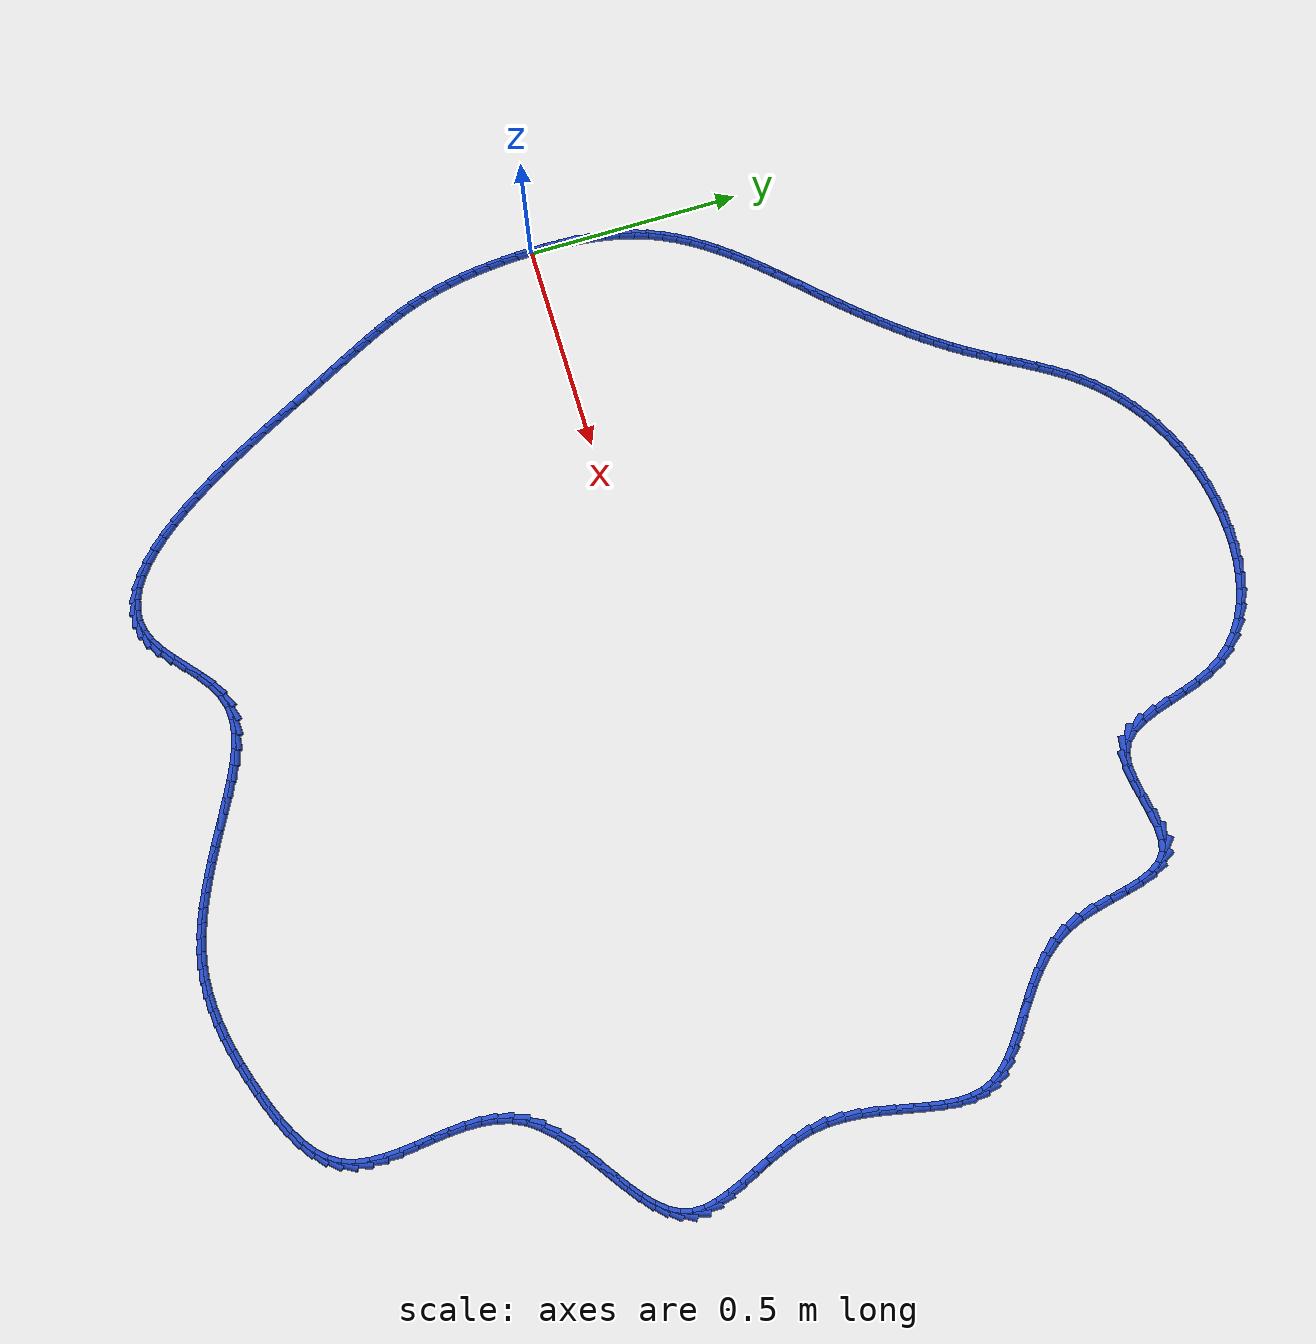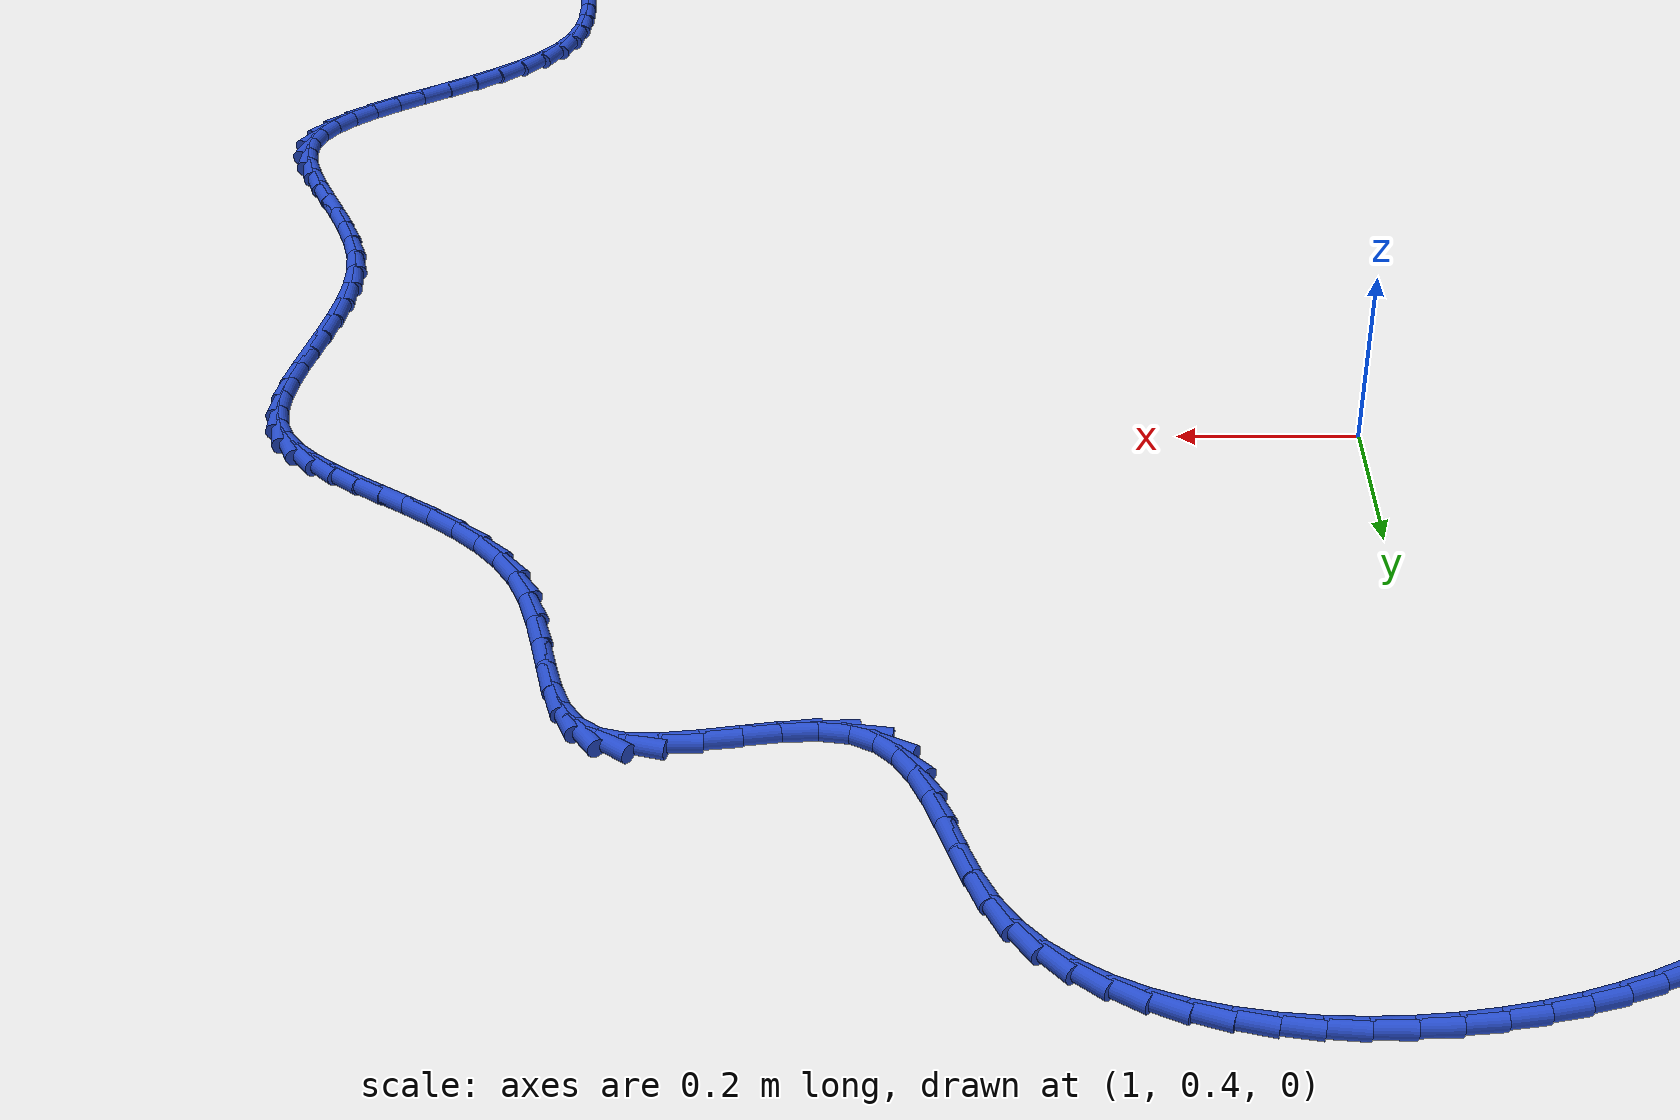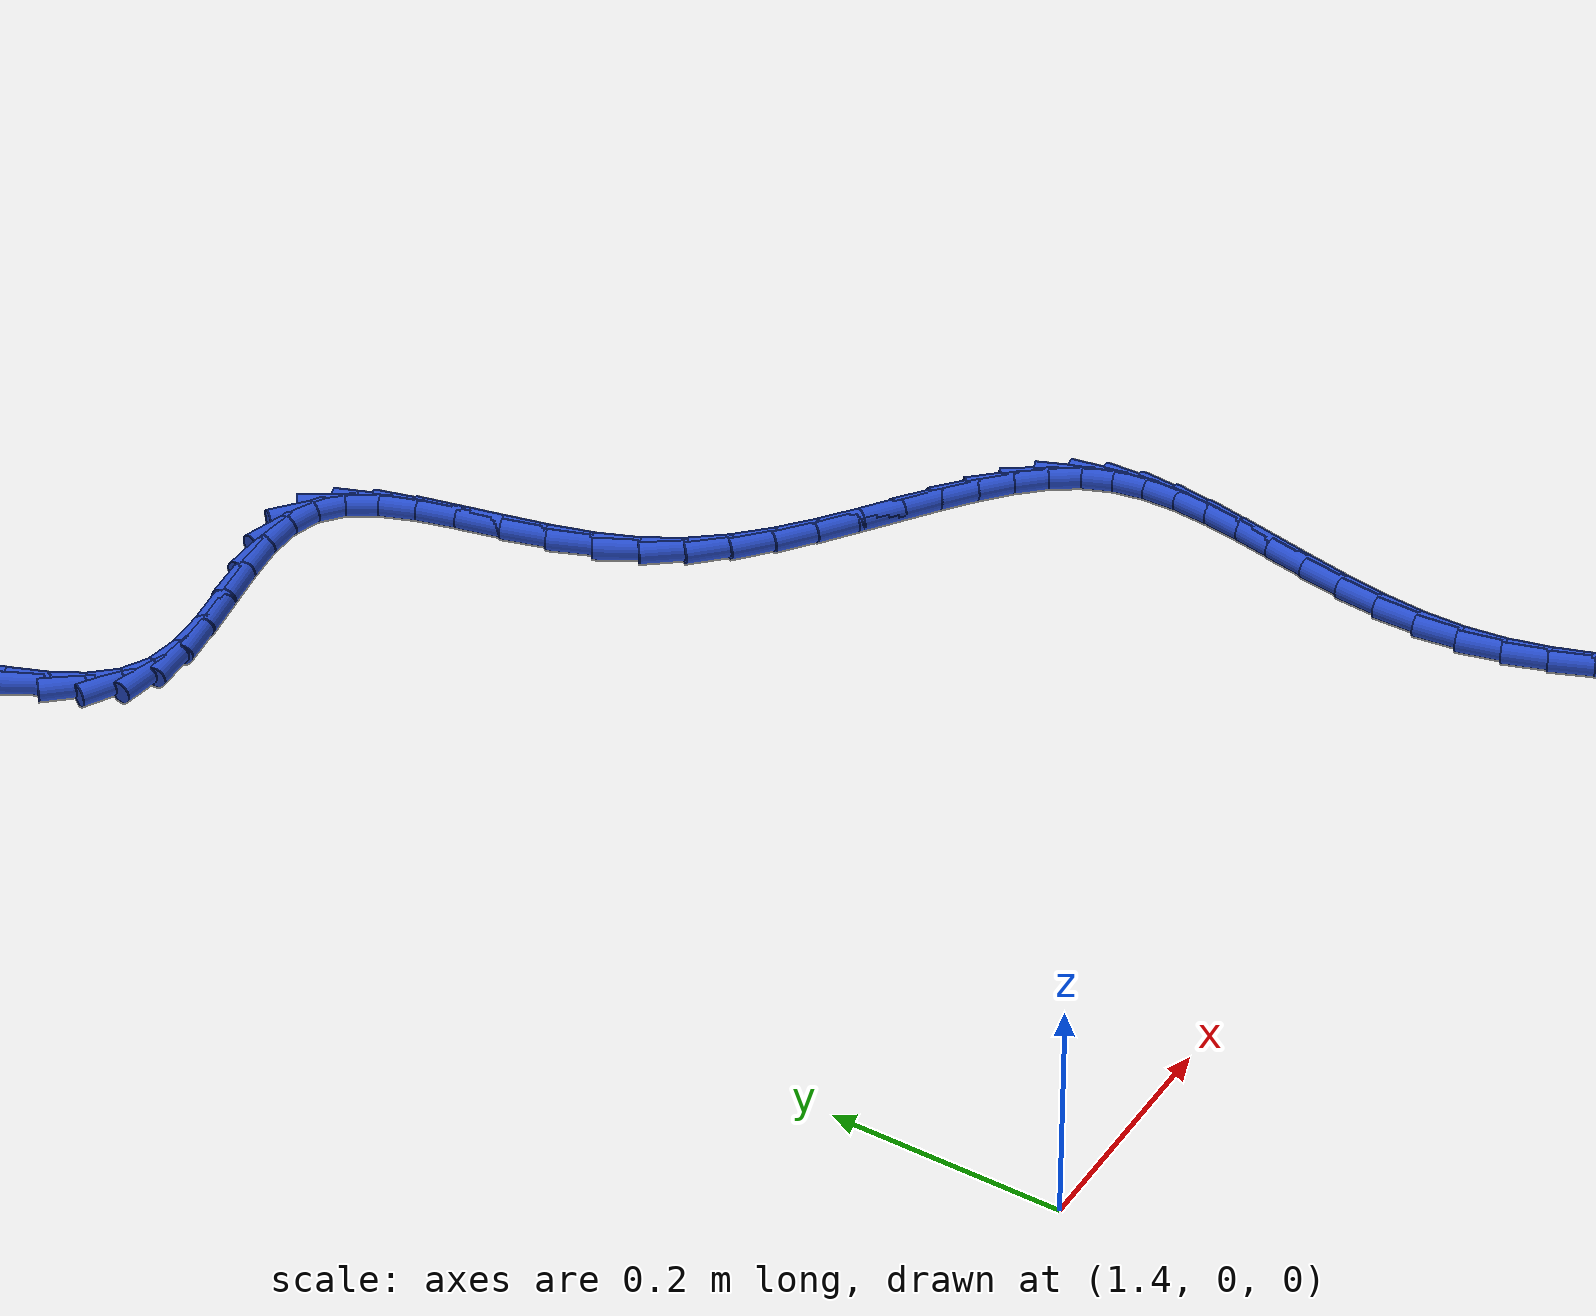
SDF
<sdf version="1.6">
 <world name="default">
  <light name="sun" type="directional">
   <pose>0 0 10 0 -0 0</pose>
   <diffuse>0.8 0.8 0.8 1</diffuse>
   <specular>0.2 0.2 0.2 1</specular>
   <attenuation>
    <range>1000</range>
    <constant>0.9</constant>
    <linear>0.01</linear>
    <quadratic>0.001</quadratic>
   </attenuation>
   <direction>-0.5 0.1 -0.9</direction>
  </light>
  <model name="ground_plane">
   <static>1</static>
   <link name="link">
    <collision name="collision">
     <geometry><plane><normal>0 0 1</normal><size>100 100</size></plane></geometry>
     <surface><friction><ode><mu>100</mu><mu2>50</mu2></ode></friction></surface>
    </collision>
    <visual name="visual">
     <cast_shadows>0</cast_shadows>
     <geometry><plane><normal>0 0 1</normal><size>100 100</size></plane></geometry>
     <material>
      <script><uri>file://media/materials/scripts/gazebo.material</uri><name>Gazebo/WhiteGlow</name></script>
     </material>
    </visual>
   </link>
  </model>
  <gravity>0 0 -9.8</gravity>
  <magnetic_field>6e-06 2.3e-05 -4.2e-05</magnetic_field>
  <atmosphere type="adiabatic"/>
  <physics name="default_physics" default="0" type="ode">
   <max_step_size>0.001</max_step_size>
   <real_time_factor>1</real_time_factor>
   <real_time_update_rate>1000</real_time_update_rate>
  </physics>
  <scene><ambient>0.4 0.4 0.4 1</ambient><background>0.7 0.7 0.7 1</background><shadows>1</shadows></scene>
  <spherical_coordinates>
   <surface_model>EARTH_WGS84</surface_model>
   <latitude_deg>0</latitude_deg>
   <longitude_deg>0</longitude_deg>
   <elevation>0</elevation>
   <heading_deg>0</heading_deg>
  </spherical_coordinates>
  <model name="line">
   <link name="link_0">
    <pose>2.168404344971009e-18 -2.0816681711721685e-17 0.01 0 1.57 -1.5666137799620388</pose>
    <collision name="collision">
     <geometry><cylinder><radius>0.01</radius><length>0.08</length></cylinder></geometry>
    </collision>
    <visual name="visual">
     <material>
      <script><name>Gazebo/Blue</name><uri>file://media/materials/scripts/gazebo.material</uri></script>
     </material>
     <geometry><cylinder><radius>0.01</radius><length>0.08</length></cylinder></geometry>
    </visual>
   </link>
   <link name="link_1">
    <pose>-0.00014931991068801466 0.03570050639835543 0.01 0 1.57 1.5447862486688388</pose>
    <collision name="collision">
     <geometry><cylinder><radius>0.01</radius><length>0.08</length></cylinder></geometry>
    </collision>
    <visual name="visual">
     <material>
      <script><name>Gazebo/Blue</name><uri>file://media/materials/scripts/gazebo.material</uri></script>
     </material>
     <geometry><cylinder><radius>0.01</radius><length>0.08</length></cylinder></geometry>
    </visual>
   </link>
   <link name="link_2">
    <pose>0.0007764572397612806 0.07128549642963346 0.01 0 1.57 1.509629643829701</pose>
    <collision name="collision">
     <geometry><cylinder><radius>0.01</radius><length>0.08</length></cylinder></geometry>
    </collision>
    <visual name="visual">
     <material>
      <script><name>Gazebo/Blue</name><uri>file://media/materials/scripts/gazebo.material</uri></script>
     </material>
     <geometry><cylinder><radius>0.01</radius><length>0.08</length></cylinder></geometry>
    </visual>
   </link>
   <link name="link_3">
    <pose>0.002941073291581074 0.10663016014580813 0.01 0 1.57 1.4691681011994149</pose>
    <collision name="collision">
     <geometry><cylinder><radius>0.01</radius><length>0.08</length></cylinder></geometry>
    </collision>
    <visual name="visual">
     <material>
      <script><name>Gazebo/Blue</name><uri>file://media/materials/scripts/gazebo.material</uri></script>
     </material>
     <geometry><cylinder><radius>0.01</radius><length>0.08</length></cylinder></geometry>
    </visual>
   </link>
   <link name="link_4">
    <pose>0.006508270085004558 0.1416096875988536 0.01 0 1.57 1.4230384902590512</pose>
    <collision name="collision">
     <geometry><cylinder><radius>0.01</radius><length>0.08</length></cylinder></geometry>
    </collision>
    <visual name="visual">
     <material>
      <script><name>Gazebo/Blue</name><uri>file://media/materials/scripts/gazebo.material</uri></script>
     </material>
     <geometry><cylinder><radius>0.01</radius><length>0.08</length></cylinder></geometry>
    </visual>
   </link>
   <link name="link_5">
    <pose>0.011641789460264932 0.17609926884074395 0.01 0 1.57 1.3708865889503392</pose>
    <collision name="collision">
     <geometry><cylinder><radius>0.01</radius><length>0.08</length></cylinder></geometry>
    </collision>
    <visual name="visual">
     <material>
      <script><name>Gazebo/Blue</name><uri>file://media/materials/scripts/gazebo.material</uri></script>
     </material>
     <geometry><cylinder><radius>0.01</radius><length>0.08</length></cylinder></geometry>
    </visual>
   </link>
   <link name="link_6">
    <pose>0.01850537325759537 0.20997409392345323 0.01 0 1.57 1.312412080597748</pose>
    <collision name="collision">
     <geometry><cylinder><radius>0.01</radius><length>0.08</length></cylinder></geometry>
    </collision>
    <visual name="visual">
     <material>
      <script><name>Gazebo/Blue</name><uri>file://media/materials/scripts/gazebo.material</uri></script>
     </material>
     <geometry><cylinder><radius>0.01</radius><length>0.08</length></cylinder></geometry>
    </visual>
   </link>
   <link name="link_7">
    <pose>0.02726276331722908 0.24310935289895558 0.01 0 1.57 1.2474297237642613</pose>
    <collision name="collision">
     <geometry><cylinder><radius>0.01</radius><length>0.08</length></cylinder></geometry>
    </collision>
    <visual name="visual">
     <material>
      <script><name>Gazebo/Blue</name><uri>file://media/materials/scripts/gazebo.material</uri></script>
     </material>
     <geometry><cylinder><radius>0.01</radius><length>0.08</length></cylinder></geometry>
    </visual>
   </link>
   <link name="link_8">
    <pose>0.03807770147939925 0.2753802358192252 0.01 0 1.57 1.1770028223140747</pose>
    <collision name="collision">
     <geometry><cylinder><radius>0.01</radius><length>0.08</length></cylinder></geometry>
    </collision>
    <visual name="visual">
     <material>
      <script><name>Gazebo/Blue</name><uri>file://media/materials/scripts/gazebo.material</uri></script>
     </material>
     <geometry><cylinder><radius>0.01</radius><length>0.08</length></cylinder></geometry>
    </visual>
   </link>
   <link name="link_9">
    <pose>0.0510826033534428 0.30667991431961295 0.01 0 1.57 1.109309502528066</pose>
    <collision name="collision">
     <geometry><cylinder><radius>0.01</radius><length>0.08</length></cylinder></geometry>
    </collision>
    <visual name="visual">
     <material>
      <script><name>Gazebo/Blue</name><uri>file://media/materials/scripts/gazebo.material</uri></script>
     </material>
     <geometry><cylinder><radius>0.01</radius><length>0.08</length></cylinder></geometry>
    </visual>
   </link>
   <link name="link_10">
    <pose>0.06617806148963003 0.33703462889010094 0.01 0 1.57 1.0483875146573116</pose>
    <collision name="collision">
     <geometry><cylinder><radius>0.01</radius><length>0.08</length></cylinder></geometry>
    </collision>
    <visual name="visual">
     <material>
      <script><name>Gazebo/Blue</name><uri>file://media/materials/scripts/gazebo.material</uri></script>
     </material>
     <geometry><cylinder><radius>0.01</radius><length>0.08</length></cylinder></geometry>
    </visual>
   </link>
   <link name="link_11">
    <pose>0.08316064611714269 0.3665303299182934 0.01 0 1.57 0.9945217166711843</pose>
    <collision name="collision">
     <geometry><cylinder><radius>0.01</radius><length>0.08</length></cylinder></geometry>
    </collision>
    <visual name="visual">
     <material>
      <script><name>Gazebo/Blue</name><uri>file://media/materials/scripts/gazebo.material</uri></script>
     </material>
     <geometry><cylinder><radius>0.01</radius><length>0.08</length></cylinder></geometry>
    </visual>
   </link>
   <link name="link_12">
    <pose>0.10182643424813126 0.39525325090351665 0.01 0 1.57 0.9477398968117192</pose>
    <collision name="collision">
     <geometry><cylinder><radius>0.01</radius><length>0.08</length></cylinder></geometry>
    </collision>
    <visual name="visual">
     <material>
      <script><name>Gazebo/Blue</name><uri>file://media/materials/scripts/gazebo.material</uri></script>
     </material>
     <geometry><cylinder><radius>0.01</radius><length>0.08</length></cylinder></geometry>
    </visual>
   </link>
   <link name="link_13">
    <pose>0.12197150289474602 0.42328962534509695 0.01 0 1.57 0.9079102131461442</pose>
    <collision name="collision">
     <geometry><cylinder><radius>0.01</radius><length>0.08</length></cylinder></geometry>
    </collision>
    <visual name="visual">
     <material>
      <script><name>Gazebo/Blue</name><uri>file://media/materials/scripts/gazebo.material</uri></script>
     </material>
     <geometry><cylinder><radius>0.01</radius><length>0.08</length></cylinder></geometry>
    </visual>
   </link>
   <link name="link_14">
    <pose>0.14339192906913736 0.4507256867423606 0.01 0 1.57 0.8748125549227674</pose>
    <collision name="collision">
     <geometry><cylinder><radius>0.01</radius><length>0.08</length></cylinder></geometry>
    </collision>
    <visual name="visual">
     <material>
      <script><name>Gazebo/Blue</name><uri>file://media/materials/scripts/gazebo.material</uri></script>
     </material>
     <geometry><cylinder><radius>0.01</radius><length>0.08</length></cylinder></geometry>
    </visual>
   </link>
   <link name="link_15">
    <pose>0.16588378978345567 0.4776476685946338 0.01 0 1.57 0.8481949853797409</pose>
    <collision name="collision">
     <geometry><cylinder><radius>0.01</radius><length>0.08</length></cylinder></geometry>
    </collision>
    <visual name="visual">
     <material>
      <script><name>Gazebo/Blue</name><uri>file://media/materials/scripts/gazebo.material</uri></script>
     </material>
     <geometry><cylinder><radius>0.01</radius><length>0.08</length></cylinder></geometry>
    </visual>
   </link>
   <link name="link_16">
    <pose>0.18924316204985142 0.504141804401243 0.01 0 1.57 0.8278149961226481</pose>
    <collision name="collision">
     <geometry><cylinder><radius>0.01</radius><length>0.08</length></cylinder></geometry>
    </collision>
    <visual name="visual">
     <material>
      <script><name>Gazebo/Blue</name><uri>file://media/materials/scripts/gazebo.material</uri></script>
     </material>
     <geometry><cylinder><radius>0.01</radius><length>0.08</length></cylinder></geometry>
    </visual>
   </link>
   <link name="link_17">
    <pose>0.21326612288047486 0.5302943276615144 0.01 0 1.57 0.8134678879189604</pose>
    <collision name="collision">
     <geometry><cylinder><radius>0.01</radius><length>0.08</length></cylinder></geometry>
    </collision>
    <visual name="visual">
     <material>
      <script><name>Gazebo/Blue</name><uri>file://media/materials/scripts/gazebo.material</uri></script>
     </material>
     <geometry><cylinder><radius>0.01</radius><length>0.08</length></cylinder></geometry>
    </visual>
   </link>
   <link name="link_18">
    <pose>0.2377487492874765 0.5561914718747744 0.01 0 1.57 0.805005337333097</pose>
    <collision name="collision">
     <geometry><cylinder><radius>0.01</radius><length>0.08</length></cylinder></geometry>
    </collision>
    <visual name="visual">
     <material>
      <script><name>Gazebo/Blue</name><uri>file://media/materials/scripts/gazebo.material</uri></script>
     </material>
     <geometry><cylinder><radius>0.01</radius><length>0.08</length></cylinder></geometry>
    </visual>
   </link>
   <link name="link_19">
    <pose>0.2624871182830065 0.5819194705403488 0.01 0 1.57 0.8023469389558977</pose>
    <collision name="collision">
     <geometry><cylinder><radius>0.01</radius><length>0.08</length></cylinder></geometry>
    </collision>
    <visual name="visual">
     <material>
      <script><name>Gazebo/Blue</name><uri>file://media/materials/scripts/gazebo.material</uri></script>
     </material>
     <geometry><cylinder><radius>0.01</radius><length>0.08</length></cylinder></geometry>
    </visual>
   </link>
   <link name="link_20">
    <pose>0.2872773068792155 0.6075645571575645 0.01 0 1.57 0.8054867972096207</pose>
    <collision name="collision">
     <geometry><cylinder><radius>0.01</radius><length>0.08</length></cylinder></geometry>
    </collision>
    <visual name="visual">
     <material>
      <script><name>Gazebo/Blue</name><uri>file://media/materials/scripts/gazebo.material</uri></script>
     </material>
     <geometry><cylinder><radius>0.01</radius><length>0.08</length></cylinder></geometry>
    </visual>
   </link>
   <link name="link_21">
    <pose>0.31191539208825364 0.6332129652257473 0.01 0 1.57 0.8142932229291717</pose>
    <collision name="collision">
     <geometry><cylinder><radius>0.01</radius><length>0.08</length></cylinder></geometry>
    </collision>
    <visual name="visual">
     <material>
      <script><name>Gazebo/Blue</name><uri>file://media/materials/scripts/gazebo.material</uri></script>
     </material>
     <geometry><cylinder><radius>0.01</radius><length>0.08</length></cylinder></geometry>
    </visual>
   </link>
   <link name="link_22">
    <pose>0.33620566093731313 0.6589491539790912 0.01 0 1.57 0.8264717777717585</pose>
    <collision name="collision">
     <geometry><cylinder><radius>0.01</radius><length>0.08</length></cylinder></geometry>
    </collision>
    <visual name="visual">
     <material>
      <script><name>Gazebo/Blue</name><uri>file://media/materials/scripts/gazebo.material</uri></script>
     </material>
     <geometry><cylinder><radius>0.01</radius><length>0.08</length></cylinder></geometry>
    </visual>
   </link>
   <link name="link_23">
    <pose>0.36004934974041697 0.6848366309557953 0.01 0 1.57 0.8404883851443289</pose>
    <collision name="collision">
     <geometry><cylinder><radius>0.01</radius><length>0.08</length></cylinder></geometry>
    </collision>
    <visual name="visual">
     <material>
      <script><name>Gazebo/Blue</name><uri>file://media/materials/scripts/gazebo.material</uri></script>
     </material>
     <geometry><cylinder><radius>0.01</radius><length>0.08</length></cylinder></geometry>
    </visual>
   </link>
   <link name="link_24">
    <pose>0.38341096625520915 0.7109252301117648 0.01 0 1.57 0.856321380373999</pose>
    <collision name="collision">
     <geometry><cylinder><radius>0.01</radius><length>0.08</length></cylinder></geometry>
    </collision>
    <visual name="visual">
     <material>
      <script><name>Gazebo/Blue</name><uri>file://media/materials/scripts/gazebo.material</uri></script>
     </material>
     <geometry><cylinder><radius>0.01</radius><length>0.08</length></cylinder></geometry>
    </visual>
   </link>
   <link name="link_25">
    <pose>0.40625610575094306 0.737264550380932 0.01 0 1.57 0.8739669154203803</pose>
    <collision name="collision">
     <geometry><cylinder><radius>0.01</radius><length>0.08</length></cylinder></geometry>
    </collision>
    <visual name="visual">
     <material>
      <script><name>Gazebo/Blue</name><uri>file://media/materials/scripts/gazebo.material</uri></script>
     </material>
     <geometry><cylinder><radius>0.01</radius><length>0.08</length></cylinder></geometry>
    </visual>
   </link>
   <link name="link_26">
    <pose>0.4285503634968722 0.7639041906972294 0.01 0 1.57 0.8934103848790669</pose>
    <collision name="collision">
     <geometry><cylinder><radius>0.01</radius><length>0.08</length></cylinder></geometry>
    </collision>
    <visual name="visual">
     <material>
      <script><name>Gazebo/Blue</name><uri>file://media/materials/scripts/gazebo.material</uri></script>
     </material>
     <geometry><cylinder><radius>0.01</radius><length>0.08</length></cylinder></geometry>
    </visual>
   </link>
   <link name="link_27">
    <pose>0.45025933476225016 0.7908937499945897 0.01 0 1.57 0.9146247005952302</pose>
    <collision name="collision">
     <geometry><cylinder><radius>0.01</radius><length>0.08</length></cylinder></geometry>
    </collision>
    <visual name="visual">
     <material>
      <script><name>Gazebo/Blue</name><uri>file://media/materials/scripts/gazebo.material</uri></script>
     </material>
     <geometry><cylinder><radius>0.01</radius><length>0.08</length></cylinder></geometry>
    </visual>
   </link>
   <link name="link_28">
    <pose>0.4713486148163302 0.8182828272069447 0.01 0 1.57 0.9375685905325318</pose>
    <collision name="collision">
     <geometry><cylinder><radius>0.01</radius><length>0.08</length></cylinder></geometry>
    </collision>
    <visual name="visual">
     <material>
      <script><name>Gazebo/Blue</name><uri>file://media/materials/scripts/gazebo.material</uri></script>
     </material>
     <geometry><cylinder><radius>0.01</radius><length>0.08</length></cylinder></geometry>
    </visual>
   </link>
   <link name="link_29">
    <pose>0.4917837989283662 0.8461210212682273 0.01 0 1.57 0.9621850253438162</pose>
    <collision name="collision">
     <geometry><cylinder><radius>0.01</radius><length>0.08</length></cylinder></geometry>
    </collision>
    <visual name="visual">
     <material>
      <script><name>Gazebo/Blue</name><uri>file://media/materials/scripts/gazebo.material</uri></script>
     </material>
     <geometry><cylinder><radius>0.01</radius><length>0.08</length></cylinder></geometry>
    </visual>
   </link>
   <link name="link_30">
    <pose>0.5115304823676114 0.8744579311123699 0.01 0 1.57 0.9883998947306946</pose>
    <collision name="collision">
     <geometry><cylinder><radius>0.01</radius><length>0.08</length></cylinder></geometry>
    </collision>
    <visual name="visual">
     <material>
      <script><name>Gazebo/Blue</name><uri>file://media/materials/scripts/gazebo.material</uri></script>
     </material>
     <geometry><cylinder><radius>0.01</radius><length>0.08</length></cylinder></geometry>
    </visual>
   </link>
   <link name="link_31">
    <pose>0.5305542604033195 0.903343155673305 0.01 0 1.57 1.0161065852240692</pose>
    <collision name="collision">
     <geometry><cylinder><radius>0.01</radius><length>0.08</length></cylinder></geometry>
    </collision>
    <visual name="visual">
     <material>
      <script><name>Gazebo/Blue</name><uri>file://media/materials/scripts/gazebo.material</uri></script>
     </material>
     <geometry><cylinder><radius>0.01</radius><length>0.08</length></cylinder></geometry>
    </visual>
   </link>
   <link name="link_32">
    <pose>0.548821112902177 0.932825960905743 0.01 0 1.57 1.0412793506993445</pose>
    <collision name="collision">
     <geometry><cylinder><radius>0.01</radius><length>0.08</length></cylinder></geometry>
    </collision>
    <visual name="visual">
     <material>
      <script><name>Gazebo/Blue</name><uri>file://media/materials/scripts/gazebo.material</uri></script>
     </material>
     <geometry><cylinder><radius>0.01</radius><length>0.08</length></cylinder></geometry>
    </visual>
   </link>
   <link name="link_33">
    <pose>0.5664018999330775 0.9628648089131729 0.01 0 1.57 1.0547561598987694</pose>
    <collision name="collision">
     <geometry><cylinder><radius>0.01</radius><length>0.08</length></cylinder></geometry>
    </collision>
    <visual name="visual">
     <material>
      <script><name>Gazebo/Blue</name><uri>file://media/materials/scripts/gazebo.material</uri></script>
     </material>
     <geometry><cylinder><radius>0.01</radius><length>0.08</length></cylinder></geometry>
    </visual>
   </link>
   <link name="link_34">
    <pose>0.5836141434641883 0.993204605284772 0.01 0 1.57 1.0553595744026218</pose>
    <collision name="collision">
     <geometry><cylinder><radius>0.01</radius><length>0.08</length></cylinder></geometry>
    </collision>
    <visual name="visual">
     <material>
      <script><name>Gazebo/Blue</name><uri>file://media/materials/scripts/gazebo.material</uri></script>
     </material>
     <geometry><cylinder><radius>0.01</radius><length>0.08</length></cylinder></geometry>
    </visual>
   </link>
   <link name="link_35">
    <pose>0.6008107950556537 1.023559581151323 0.01 0 1.57 1.0430992853419483</pose>
    <collision name="collision">
     <geometry><cylinder><radius>0.01</radius><length>0.08</length></cylinder></geometry>
    </collision>
    <visual name="visual">
     <material>
      <script><name>Gazebo/Blue</name><uri>file://media/materials/scripts/gazebo.material</uri></script>
     </material>
     <geometry><cylinder><radius>0.01</radius><length>0.08</length></cylinder></geometry>
    </visual>
   </link>
   <link name="link_36">
    <pose>0.6183448062676196 1.0536439676436111 0.01 0 1.57 1.0178349097681956</pose>
    <collision name="collision">
     <geometry><cylinder><radius>0.01</radius><length>0.08</length></cylinder></geometry>
    </collision>
    <visual name="visual">
     <material>
      <script><name>Gazebo/Blue</name><uri>file://media/materials/scripts/gazebo.material</uri></script>
     </material>
     <geometry><cylinder><radius>0.01</radius><length>0.08</length></cylinder></geometry>
    </visual>
   </link>
   <link name="link_37">
    <pose>0.6365691286602302 1.0831719958924189 0.01 0 1.57 0.9793348463738109</pose>
    <collision name="collision">
     <geometry><cylinder><radius>0.01</radius><length>0.08</length></cylinder></geometry>
    </collision>
    <visual name="visual">
     <material>
      <script><name>Gazebo/Blue</name><uri>file://media/materials/scripts/gazebo.material</uri></script>
     </material>
     <geometry><cylinder><radius>0.01</radius><length>0.08</length></cylinder></geometry>
    </visual>
   </link>
   <link name="link_38">
    <pose>0.6558367137936312 1.1118578970285313 0.01 0 1.57 0.9274199164957214</pose>
    <collision name="collision">
     <geometry><cylinder><radius>0.01</radius><length>0.08</length></cylinder></geometry>
    </collision>
    <visual name="visual">
     <material>
      <script><name>Gazebo/Blue</name><uri>file://media/materials/scripts/gazebo.material</uri></script>
     </material>
     <geometry><cylinder><radius>0.01</radius><length>0.08</length></cylinder></geometry>
    </visual>
   </link>
   <link name="link_39">
    <pose>0.676500041516095 1.139416159309446 0.01 0 1.57 0.8657220078432462</pose>
    <collision name="collision">
     <geometry><cylinder><radius>0.01</radius><length>0.08</length></cylinder></geometry>
    </collision>
    <visual name="visual">
     <material>
      <script><name>Gazebo/Blue</name><uri>file://media/materials/scripts/gazebo.material</uri></script>
     </material>
     <geometry><cylinder><radius>0.01</radius><length>0.08</length></cylinder></geometry>
    </visual>
   </link>
   <link name="link_40">
    <pose>0.6988008850189337 1.1656216163870563 0.01 0 1.57 0.8025951879977177</pose>
    <collision name="collision">
     <geometry><cylinder><radius>0.01</radius><length>0.08</length></cylinder></geometry>
    </collision>
    <visual name="visual">
     <material>
      <script><name>Gazebo/Blue</name><uri>file://media/materials/scripts/gazebo.material</uri></script>
     </material>
     <geometry><cylinder><radius>0.01</radius><length>0.08</length></cylinder></geometry>
    </visual>
   </link>
   <link name="link_41">
    <pose>0.7227285406261549 1.1903867252193103 0.01 0 1.57 0.7392416002955182</pose>
    <collision name="collision">
     <geometry><cylinder><radius>0.01</radius><length>0.08</length></cylinder></geometry>
    </collision>
    <visual name="visual">
     <material>
      <script><name>Gazebo/Blue</name><uri>file://media/materials/scripts/gazebo.material</uri></script>
     </material>
     <geometry><cylinder><radius>0.01</radius><length>0.08</length></cylinder></geometry>
    </visual>
   </link>
   <link name="link_42">
    <pose>0.7482372778181804 1.2136430356421155 0.01 0 1.57 0.6757275125268553</pose>
    <collision name="collision">
     <geometry><cylinder><radius>0.01</radius><length>0.08</length></cylinder></geometry>
    </collision>
    <visual name="visual">
     <material>
      <script><name>Gazebo/Blue</name><uri>file://media/materials/scripts/gazebo.material</uri></script>
     </material>
     <geometry><cylinder><radius>0.01</radius><length>0.08</length></cylinder></geometry>
    </visual>
   </link>
   <link name="link_43">
    <pose>0.7752813660754317 1.235322097491378 0.01 0 1.57 0.6121303590094614</pose>
    <collision name="collision">
     <geometry><cylinder><radius>0.01</radius><length>0.08</length></cylinder></geometry>
    </collision>
    <visual name="visual">
     <material>
      <script><name>Gazebo/Blue</name><uri>file://media/materials/scripts/gazebo.material</uri></script>
     </material>
     <geometry><cylinder><radius>0.01</radius><length>0.08</length></cylinder></geometry>
    </visual>
   </link>
   <link name="link_44">
    <pose>0.8038150748783308 1.2553554606030048 0.01 0 1.57 0.5485389703150327</pose>
    <collision name="collision">
     <geometry><cylinder><radius>0.01</radius><length>0.08</length></cylinder></geometry>
    </collision>
    <visual name="visual">
     <material>
      <script><name>Gazebo/Blue</name><uri>file://media/materials/scripts/gazebo.material</uri></script>
     </material>
     <geometry><cylinder><radius>0.01</radius><length>0.08</length></cylinder></geometry>
    </visual>
   </link>
   <link name="link_45">
    <pose>0.8337926737072988 1.2736746748129029 0.01 0 1.57 0.48505324241310743</pose>
    <collision name="collision">
     <geometry><cylinder><radius>0.01</radius><length>0.08</length></cylinder></geometry>
    </collision>
    <visual name="visual">
     <material>
      <script><name>Gazebo/Blue</name><uri>file://media/materials/scripts/gazebo.material</uri></script>
     </material>
     <geometry><cylinder><radius>0.01</radius><length>0.08</length></cylinder></geometry>
    </visual>
   </link>
   <link name="link_46">
    <pose>0.8651684320427577 1.290211289956979 0.01 0 1.57 0.42178321167562166</pose>
    <collision name="collision">
     <geometry><cylinder><radius>0.01</radius><length>0.08</length></cylinder></geometry>
    </collision>
    <visual name="visual">
     <material>
      <script><name>Gazebo/Blue</name><uri>file://media/materials/scripts/gazebo.material</uri></script>
     </material>
     <geometry><cylinder><radius>0.01</radius><length>0.08</length></cylinder></geometry>
    </visual>
   </link>
   <link name="link_47">
    <pose>0.8978966193651292 1.304896855871141 0.01 0 1.57 0.3588475425762844</pose>
    <collision name="collision">
     <geometry><cylinder><radius>0.01</radius><length>0.08</length></cylinder></geometry>
    </collision>
    <visual name="visual">
     <material>
      <script><name>Gazebo/Blue</name><uri>file://media/materials/scripts/gazebo.material</uri></script>
     </material>
     <geometry><cylinder><radius>0.01</radius><length>0.08</length></cylinder></geometry>
    </visual>
   </link>
   <link name="link_48">
    <pose>0.9319315051548348 1.3176629223912948 0.01 0 1.57 0.2963714794348459</pose>
    <collision name="collision">
     <geometry><cylinder><radius>0.01</radius><length>0.08</length></cylinder></geometry>
    </collision>
    <visual name="visual">
     <material>
      <script><name>Gazebo/Blue</name><uri>file://media/materials/scripts/gazebo.material</uri></script>
     </material>
     <geometry><cylinder><radius>0.01</radius><length>0.08</length></cylinder></geometry>
    </visual>
   </link>
   <link name="link_49">
    <pose>0.9672273588922964 1.3284410393533477 0.01 0 1.57 0.23448433996915305</pose>
    <collision name="collision">
     <geometry><cylinder><radius>0.01</radius><length>0.08</length></cylinder></geometry>
    </collision>
    <visual name="visual">
     <material>
      <script><name>Gazebo/Blue</name><uri>file://media/materials/scripts/gazebo.material</uri></script>
     </material>
     <geometry><cylinder><radius>0.01</radius><length>0.08</length></cylinder></geometry>
    </visual>
   </link>
   <link name="link_50">
    <pose>1.0037384188946852 1.3371627484764115 0.01 0 1.57 0.1731466406709943</pose>
    <collision name="collision">
     <geometry><cylinder><radius>0.01</radius><length>0.08</length></cylinder></geometry>
    </collision>
    <visual name="visual">
     <material>
      <script><name>Gazebo/Blue</name><uri>file://media/materials/scripts/gazebo.material</uri></script>
     </material>
     <geometry><cylinder><radius>0.01</radius><length>0.08</length></cylinder></geometry>
    </visual>
   </link>
   <link name="link_51">
    <pose>1.0413417840081922 1.3437394996967627 0.01 0 1.57 0.11119973759189969</pose>
    <collision name="collision">
     <geometry><cylinder><radius>0.01</radius><length>0.08</length></cylinder></geometry>
    </collision>
    <visual name="visual">
     <material>
      <script><name>Gazebo/Blue</name><uri>file://media/materials/scripts/gazebo.material</uri></script>
     </material>
     <geometry><cylinder><radius>0.01</radius><length>0.08</length></cylinder></geometry>
    </visual>
   </link>
   <link name="link_52">
    <pose>1.0796713137847698 1.3480193887298757 0.01 0 1.57 0.04703011918606339</pose>
    <collision name="collision">
     <geometry><cylinder><radius>0.01</radius><length>0.08</length></cylinder></geometry>
    </collision>
    <visual name="visual">
     <material>
      <script><name>Gazebo/Blue</name><uri>file://media/materials/scripts/gazebo.material</uri></script>
     </material>
     <geometry><cylinder><radius>0.01</radius><length>0.08</length></cylinder></geometry>
    </visual>
   </link>
   <link name="link_53">
    <pose>1.1183130434315705 1.34983805493992 0.01 0 1.57 -0.020934097310999548</pose>
    <collision name="collision">
     <geometry><cylinder><radius>0.01</radius><length>0.08</length></cylinder></geometry>
    </collision>
    <visual name="visual">
     <material>
      <script><name>Gazebo/Blue</name><uri>file://media/materials/scripts/gazebo.material</uri></script>
     </material>
     <geometry><cylinder><radius>0.01</radius><length>0.08</length></cylinder></geometry>
    </visual>
   </link>
   <link name="link_54">
    <pose>1.1568530081557467 1.3490311376910662 0.01 0 1.57 -0.09431328008556371</pose>
    <collision name="collision">
     <geometry><cylinder><radius>0.01</radius><length>0.08</length></cylinder></geometry>
    </collision>
    <visual name="visual">
     <material>
      <script><name>Gazebo/Blue</name><uri>file://media/materials/scripts/gazebo.material</uri></script>
     </material>
     <geometry><cylinder><radius>0.01</radius><length>0.08</length></cylinder></geometry>
    </visual>
   </link>
   <link name="link_55">
    <pose>1.1948772431644508 1.345434276347483 0.01 0 1.57 -0.17480476393260974</pose>
    <collision name="collision">
     <geometry><cylinder><radius>0.01</radius><length>0.08</length></cylinder></geometry>
    </collision>
    <visual name="visual">
     <material>
      <script><name>Gazebo/Blue</name><uri>file://media/materials/scripts/gazebo.material</uri></script>
     </material>
     <geometry><cylinder><radius>0.01</radius><length>0.08</length></cylinder></geometry>
    </visual>
   </link>
   <link name="link_56">
    <pose>1.2319717836648358 1.3388831102733407 0.01 0 1.57 -0.2641574221111155</pose>
    <collision name="collision">
     <geometry><cylinder><radius>0.01</radius><length>0.08</length></cylinder></geometry>
    </collision>
    <visual name="visual">
     <material>
      <script><name>Gazebo/Blue</name><uri>file://media/materials/scripts/gazebo.material</uri></script>
     </material>
     <geometry><cylinder><radius>0.01</radius><length>0.08</length></cylinder></geometry>
    </visual>
   </link>
   <link name="link_57">
    <pose>1.2677226648640547 1.3292132788328093 0.01 0 1.57 -0.3640571839372722</pose>
    <collision name="collision">
     <geometry><cylinder><radius>0.01</radius><length>0.08</length></cylinder></geometry>
    </collision>
    <visual name="visual">
     <material>
      <script><name>Gazebo/Blue</name><uri>file://media/materials/scripts/gazebo.material</uri></script>
     </material>
     <geometry><cylinder><radius>0.01</radius><length>0.08</length></cylinder></geometry>
    </visual>
   </link>
   <link name="link_58">
    <pose>1.3017159219692587 1.3162604213900584 0.01 0 1.57 -0.47587558719633277</pose>
    <collision name="collision">
     <geometry><cylinder><radius>0.01</radius><length>0.08</length></cylinder></geometry>
    </collision>
    <visual name="visual">
     <material>
      <script><name>Gazebo/Blue</name><uri>file://media/materials/scripts/gazebo.material</uri></script>
     </material>
     <geometry><cylinder><radius>0.01</radius><length>0.08</length></cylinder></geometry>
    </visual>
   </link>
   <link name="link_59">
    <pose>1.3335375901876017 1.299860177309258 0.01 0 1.57 -0.6002443509306218</pose>
    <collision name="collision">
     <geometry><cylinder><radius>0.01</radius><length>0.08</length></cylinder></geometry>
    </collision>
    <visual name="visual">
     <material>
      <script><name>Gazebo/Blue</name><uri>file://media/materials/scripts/gazebo.material</uri></script>
     </material>
     <geometry><cylinder><radius>0.01</radius><length>0.08</length></cylinder></geometry>
    </visual>
   </link>
   <link name="link_60">
    <pose>1.3627737047262347 1.2798481859545772 0.01 0 1.57 -0.736491432162217</pose>
    <collision name="collision">
     <geometry><cylinder><radius>0.01</radius><length>0.08</length></cylinder></geometry>
    </collision>
    <visual name="visual">
     <material>
      <script><name>Gazebo/Blue</name><uri>file://media/materials/scripts/gazebo.material</uri></script>
     </material>
     <geometry><cylinder><radius>0.01</radius><length>0.08</length></cylinder></geometry>
    </visual>
   </link>
   <link name="link_61">
    <pose>1.3890103007923118 1.2560600866901865 0.01 0 1.57 -0.882133702780651</pose>
    <collision name="collision">
     <geometry><cylinder><radius>0.01</radius><length>0.08</length></cylinder></geometry>
    </collision>
    <visual name="visual">
     <material>
      <script><name>Gazebo/Blue</name><uri>file://media/materials/scripts/gazebo.material</uri></script>
     </material>
     <geometry><cylinder><radius>0.01</radius><length>0.08</length></cylinder></geometry>
    </visual>
   </link>
   <link name="link_62">
    <pose>1.4118334135929844 1.2283315188802557 0.01 0 1.57 -1.0326805408324085</pose>
    <collision name="collision">
     <geometry><cylinder><radius>0.01</radius><length>0.08</length></cylinder></geometry>
    </collision>
    <visual name="visual">
     <material>
      <script><name>Gazebo/Blue</name><uri>file://media/materials/scripts/gazebo.material</uri></script>
     </material>
     <geometry><cylinder><radius>0.01</radius><length>0.08</length></cylinder></geometry>
    </visual>
   </link>
   <link name="link_63">
    <pose>1.4308319617072212 1.1965012915856983 0.01 0 1.57 -1.1648842897388751</pose>
    <collision name="collision">
     <geometry><cylinder><radius>0.01</radius><length>0.08</length></cylinder></geometry>
    </collision>
    <visual name="visual">
     <material>
      <script><name>Gazebo/Blue</name><uri>file://media/materials/scripts/gazebo.material</uri></script>
     </material>
     <geometry><cylinder><radius>0.01</radius><length>0.08</length></cylinder></geometry>
    </visual>
   </link>
   <link name="link_64">
    <pose>1.4461036501958089 1.1609675239246888 0.01 0 1.57 -1.2446633629824646</pose>
    <collision name="collision">
     <geometry><cylinder><radius>0.01</radius><length>0.08</length></cylinder></geometry>
    </collision>
    <visual name="visual">
     <material>
      <script><name>Gazebo/Blue</name><uri>file://media/materials/scripts/gazebo.material</uri></script>
     </material>
     <geometry><cylinder><radius>0.01</radius><length>0.08</length></cylinder></geometry>
    </visual>
   </link>
   <link name="link_65">
    <pose>1.4588347300500655 1.1233249758627701 0.01 0 1.57 -1.2765330228267462</pose>
    <collision name="collision">
     <geometry><cylinder><radius>0.01</radius><length>0.08</length></cylinder></geometry>
    </collision>
    <visual name="visual">
     <material>
      <script><name>Gazebo/Blue</name><uri>file://media/materials/scripts/gazebo.material</uri></script>
     </material>
     <geometry><cylinder><radius>0.01</radius><length>0.08</length></cylinder></geometry>
    </visual>
   </link>
   <link name="link_66">
    <pose>1.4703517745765737 1.0853226639839069 0.01 0 1.57 -1.263240333934518</pose>
    <collision name="collision">
     <geometry><cylinder><radius>0.01</radius><length>0.08</length></cylinder></geometry>
    </collision>
    <visual name="visual">
     <material>
      <script><name>Gazebo/Blue</name><uri>file://media/materials/scripts/gazebo.material</uri></script>
     </material>
     <geometry><cylinder><radius>0.01</radius><length>0.08</length></cylinder></geometry>
    </visual>
   </link>
   <link name="link_67">
    <pose>1.4819813570819134 1.0487096048720652 0.01 0 1.57 -1.1985895858658875</pose>
    <collision name="collision">
     <geometry><cylinder><radius>0.01</radius><length>0.08</length></cylinder></geometry>
    </collision>
    <visual name="visual">
     <material>
      <script><name>Gazebo/Blue</name><uri>file://media/materials/scripts/gazebo.material</uri></script>
     </material>
     <geometry><cylinder><radius>0.01</radius><length>0.08</length></cylinder></geometry>
    </visual>
   </link>
   <link name="link_68">
    <pose>1.4950500508726665 1.0152348151112096 0.01 0 1.57 -1.0649702297724188</pose>
    <collision name="collision">
     <geometry><cylinder><radius>0.01</radius><length>0.08</length></cylinder></geometry>
    </collision>
    <visual name="visual">
     <material>
      <script><name>Gazebo/Blue</name><uri>file://media/materials/scripts/gazebo.material</uri></script>
     </material>
     <geometry><cylinder><radius>0.01</radius><length>0.08</length></cylinder></geometry>
    </visual>
   </link>
   <link name="link_69">
    <pose>1.5108844292554147 0.9866473112853061 0.01 0 1.57 -0.8337050981032906</pose>
    <collision name="collision">
     <geometry><cylinder><radius>0.01</radius><length>0.08</length></cylinder></geometry>
    </collision>
    <visual name="visual">
     <material>
      <script><name>Gazebo/Blue</name><uri>file://media/materials/scripts/gazebo.material</uri></script>
     </material>
     <geometry><cylinder><radius>0.01</radius><length>0.08</length></cylinder></geometry>
    </visual>
   </link>
   <link name="link_70">
    <pose>1.530811065536738 0.9646961099783193 0.01 0 1.57 -0.4914833316701815</pose>
    <collision name="collision">
     <geometry><cylinder><radius>0.01</radius><length>0.08</length></cylinder></geometry>
    </collision>
    <visual name="visual">
     <material>
      <script><name>Gazebo/Blue</name><uri>file://media/materials/scripts/gazebo.material</uri></script>
     </material>
     <geometry><cylinder><radius>0.01</radius><length>0.08</length></cylinder></geometry>
    </visual>
   </link>
   <link name="link_71">
    <pose>1.556155798328719 0.9511292012238209 0.01 0 1.57 -0.14231514319397232</pose>
    <collision name="collision">
     <geometry><cylinder><radius>0.01</radius><length>0.08</length></cylinder></geometry>
    </collision>
    <visual name="visual">
     <material>
      <script><name>Gazebo/Blue</name><uri>file://media/materials/scripts/gazebo.material</uri></script>
     </material>
     <geometry><cylinder><radius>0.01</radius><length>0.08</length></cylinder></geometry>
    </visual>
   </link>
   <link name="link_72">
    <pose>1.5874894284046954 0.9466395999716825 0.01 0 1.57 0.06249385432634463</pose>
    <collision name="collision">
     <geometry><cylinder><radius>0.01</radius><length>0.08</length></cylinder></geometry>
    </collision>
    <visual name="visual">
     <material>
      <script><name>Gazebo/Blue</name><uri>file://media/materials/scripts/gazebo.material</uri></script>
     </material>
     <geometry><cylinder><radius>0.01</radius><length>0.08</length></cylinder></geometry>
    </visual>
   </link>
   <link name="link_73">
    <pose>1.623202796200517 0.948874376026403 0.01 0 1.57 0.1577567117582689</pose>
    <collision name="collision">
     <geometry><cylinder><radius>0.01</radius><length>0.08</length></cylinder></geometry>
    </collision>
    <visual name="visual">
     <material>
      <script><name>Gazebo/Blue</name><uri>file://media/materials/scripts/gazebo.material</uri></script>
     </material>
     <geometry><cylinder><radius>0.01</radius><length>0.08</length></cylinder></geometry>
    </visual>
   </link>
   <link name="link_74">
    <pose>1.661295639174587 0.9549341313531258 0.01 0 1.57 0.17961237932217142</pose>
    <collision name="collision">
     <geometry><cylinder><radius>0.01</radius><length>0.08</length></cylinder></geometry>
    </collision>
    <visual name="visual">
     <material>
      <script><name>Gazebo/Blue</name><uri>file://media/materials/scripts/gazebo.material</uri></script>
     </material>
     <geometry><cylinder><radius>0.01</radius><length>0.08</length></cylinder></geometry>
    </visual>
   </link>
   <link name="link_75">
    <pose>1.6997676947853058 0.9619194679169941 0.01 0 1.57 0.1351649167424212</pose>
    <collision name="collision">
     <geometry><cylinder><radius>0.01</radius><length>0.08</length></cylinder></geometry>
    </collision>
    <visual name="visual">
     <material>
      <script><name>Gazebo/Blue</name><uri>file://media/materials/scripts/gazebo.material</uri></script>
     </material>
     <geometry><cylinder><radius>0.01</radius><length>0.08</length></cylinder></geometry>
    </visual>
   </link>
   <link name="link_76">
    <pose>1.7366187004910747 0.9669309876831511 0.01 0 1.57 0.004162064750348324</pose>
    <collision name="collision">
     <geometry><cylinder><radius>0.01</radius><length>0.08</length></cylinder></geometry>
    </collision>
    <visual name="visual">
     <material>
      <script><name>Gazebo/Blue</name><uri>file://media/materials/scripts/gazebo.material</uri></script>
     </material>
     <geometry><cylinder><radius>0.01</radius><length>0.08</length></cylinder></geometry>
    </visual>
   </link>
   <link name="link_77">
    <pose>1.7698483937502953 0.9670692926167399 0.01 0 1.57 -0.2694297465666531</pose>
    <collision name="collision">
     <geometry><cylinder><radius>0.01</radius><length>0.08</length></cylinder></geometry>
    </collision>
    <visual name="visual">
     <material>
      <script><name>Gazebo/Blue</name><uri>file://media/materials/scripts/gazebo.material</uri></script>
     </material>
     <geometry><cylinder><radius>0.01</radius><length>0.08</length></cylinder></geometry>
    </visual>
   </link>
   <link name="link_78">
    <pose>1.7974630783442147 0.9594436548518048 0.01 0 1.57 -0.6767344606360437</pose>
    <collision name="collision">
     <geometry><cylinder><radius>0.01</radius><length>0.08</length></cylinder></geometry>
    </collision>
    <visual name="visual">
     <material>
      <script><name>Gazebo/Blue</name><uri>file://media/materials/scripts/gazebo.material</uri></script>
     </material>
     <geometry><cylinder><radius>0.01</radius><length>0.08</length></cylinder></geometry>
    </visual>
   </link>
   <link name="link_79">
    <pose>1.8185097135505401 0.9425374274401372 0.01 0 1.57 -1.0072825536661352</pose>
    <collision name="collision">
     <geometry><cylinder><radius>0.01</radius><length>0.08</length></cylinder></geometry>
    </collision>
    <visual name="visual">
     <material>
      <script><name>Gazebo/Blue</name><uri>file://media/materials/scripts/gazebo.material</uri></script>
     </material>
     <geometry><cylinder><radius>0.01</radius><length>0.08</length></cylinder></geometry>
    </visual>
   </link>
   <link name="link_80">
    <pose>1.8342044959416008 0.917698223107107 0.01 0 1.57 -1.206943200504616</pose>
    <collision name="collision">
     <geometry><cylinder><radius>0.01</radius><length>0.08</length></cylinder></geometry>
    </collision>
    <visual name="visual">
     <material>
      <script><name>Gazebo/Blue</name><uri>file://media/materials/scripts/gazebo.material</uri></script>
     </material>
     <geometry><cylinder><radius>0.01</radius><length>0.08</length></cylinder></geometry>
    </visual>
   </link>
   <link name="link_81">
    <pose>1.846034852523112 0.8866317870860084 0.01 0 1.57 -1.3111584066107633</pose>
    <collision name="collision">
     <geometry><cylinder><radius>0.01</radius><length>0.08</length></cylinder></geometry>
    </collision>
    <visual name="visual">
     <material>
      <script><name>Gazebo/Blue</name><uri>file://media/materials/scripts/gazebo.material</uri></script>
     </material>
     <geometry><cylinder><radius>0.01</radius><length>0.08</length></cylinder></geometry>
    </visual>
   </link>
   <link name="link_82">
    <pose>1.8554882103007924 0.8510438646101358 0.01 0 1.57 -1.3513920573671303</pose>
    <collision name="collision">
     <geometry><cylinder><radius>0.01</radius><length>0.08</length></cylinder></geometry>
    </collision>
    <visual name="visual">
     <material>
      <script><name>Gazebo/Blue</name><uri>file://media/materials/scripts/gazebo.material</uri></script>
     </material>
     <geometry><cylinder><radius>0.01</radius><length>0.08</length></cylinder></geometry>
    </visual>
   </link>
   <link name="link_83">
    <pose>1.8640519962803581 0.8126402009127831 0.01 0 1.57 -1.3429620112486003</pose>
    <collision name="collision">
     <geometry><cylinder><radius>0.01</radius><length>0.08</length></cylinder></geometry>
    </collision>
    <visual name="visual">
     <material>
      <script><name>Gazebo/Blue</name><uri>file://media/materials/scripts/gazebo.material</uri></script>
     </material>
     <geometry><cylinder><radius>0.01</radius><length>0.08</length></cylinder></geometry>
    </visual>
   </link>
   <link name="link_84">
    <pose>1.8732136374675272 0.7731265412272458 0.01 0 1.57 -1.2894699400062954</pose>
    <collision name="collision">
     <geometry><cylinder><radius>0.01</radius><length>0.08</length></cylinder></geometry>
    </collision>
    <visual name="visual">
     <material>
      <script><name>Gazebo/Blue</name><uri>file://media/materials/scripts/gazebo.material</uri></script>
     </material>
     <geometry><cylinder><radius>0.01</radius><length>0.08</length></cylinder></geometry>
    </visual>
   </link>
   <link name="link_85">
    <pose>1.8844605608680165 0.7342086307868172 0.01 0 1.57 -1.1862220626526745</pose>
    <collision name="collision">
     <geometry><cylinder><radius>0.01</radius><length>0.08</length></cylinder></geometry>
    </collision>
    <visual name="visual">
     <material>
      <script><name>Gazebo/Blue</name><uri>file://media/materials/scripts/gazebo.material</uri></script>
     </material>
     <geometry><cylinder><radius>0.01</radius><length>0.08</length></cylinder></geometry>
    </visual>
   </link>
   <link name="link_86">
    <pose>1.8992801934875434 0.697592214824793 0.01 0 1.57 -1.0367568311186584</pose>
    <collision name="collision">
     <geometry><cylinder><radius>0.01</radius><length>0.08</length></cylinder></geometry>
    </collision>
    <visual name="visual">
     <material>
      <script><name>Gazebo/Blue</name><uri>file://media/materials/scripts/gazebo.material</uri></script>
     </material>
     <geometry><cylinder><radius>0.01</radius><length>0.08</length></cylinder></geometry>
    </visual>
   </link>
   <link name="link_87">
    <pose>1.9187741632120376 0.6646273606892414 0.01 0 1.57 -0.8953120859929183</pose>
    <collision name="collision">
     <geometry><cylinder><radius>0.01</radius><length>0.08</length></cylinder></geometry>
    </collision>
    <visual name="visual">
     <material>
      <script><name>Gazebo/Blue</name><uri>file://media/materials/scripts/gazebo.material</uri></script>
     </material>
     <geometry><cylinder><radius>0.01</radius><length>0.08</length></cylinder></geometry>
    </visual>
   </link>
   <link name="link_88">
    <pose>1.942396139450572 0.635144841473986 0.01 0 1.57 -0.781860019135283</pose>
    <collision name="collision">
     <geometry><cylinder><radius>0.01</radius><length>0.08</length></cylinder></geometry>
    </collision>
    <visual name="visual">
     <material>
      <script><name>Gazebo/Blue</name><uri>file://media/materials/scripts/gazebo.material</uri></script>
     </material>
     <geometry><cylinder><radius>0.01</radius><length>0.08</length></cylinder></geometry>
    </visual>
   </link>
   <link name="link_89">
    <pose>1.9691598576572256 0.6085698441252252 0.01 0 1.57 -0.6976487571255474</pose>
    <collision name="collision">
     <geometry><cylinder><radius>0.01</radius><length>0.08</length></cylinder></geometry>
    </collision>
    <visual name="visual">
     <material>
      <script><name>Gazebo/Blue</name><uri>file://media/materials/scripts/gazebo.material</uri></script>
     </material>
     <geometry><cylinder><radius>0.01</radius><length>0.08</length></cylinder></geometry>
    </visual>
   </link>
   <link name="link_90">
    <pose>1.9980790489629827 0.5843275516035898 0.01 0 1.57 -0.6417569368771321</pose>
    <collision name="collision">
     <geometry><cylinder><radius>0.01</radius><length>0.08</length></cylinder></geometry>
    </collision>
    <visual name="visual">
     <material>
      <script><name>Gazebo/Blue</name><uri>file://media/materials/scripts/gazebo.material</uri></script>
     </material>
     <geometry><cylinder><radius>0.01</radius><length>0.08</length></cylinder></geometry>
    </visual>
   </link>
   <link name="link_91">
    <pose>2.0281674444988287 0.5618431468697094 0.01 0 1.57 -0.6131915807693886</pose>
    <collision name="collision">
     <geometry><cylinder><radius>0.01</radius><length>0.08</length></cylinder></geometry>
    </collision>
    <visual name="visual">
     <material>
      <script><name>Gazebo/Blue</name><uri>file://media/materials/scripts/gazebo.material</uri></script>
     </material>
     <geometry><cylinder><radius>0.01</radius><length>0.08</length></cylinder></geometry>
    </visual>
   </link>
   <link name="link_92">
    <pose>2.058438775395745 0.5405418128842143 0.01 0 1.57 -0.6122157791218025</pose>
    <collision name="collision">
     <geometry><cylinder><radius>0.01</radius><length>0.08</length></cylinder></geometry>
    </collision>
    <visual name="visual">
     <material>
      <script><name>Gazebo/Blue</name><uri>file://media/materials/scripts/gazebo.material</uri></script>
     </material>
     <geometry><cylinder><radius>0.01</radius><length>0.08</length></cylinder></geometry>
    </visual>
   </link>
   <link name="link_93">
    <pose>2.087906772784719 0.5198487326077345 0.01 0 1.57 -0.6412044839459847</pose>
    <collision name="collision">
     <geometry><cylinder><radius>0.01</radius><length>0.08</length></cylinder></geometry>
    </collision>
    <visual name="visual">
     <material>
      <script><name>Gazebo/Blue</name><uri>file://media/materials/scripts/gazebo.material</uri></script>
     </material>
     <geometry><cylinder><radius>0.01</radius><length>0.08</length></cylinder></geometry>
    </visual>
   </link>
   <link name="link_94">
    <pose>2.115585167796734 0.49918908900090053 0.01 0 1.57 -0.7052833487119702</pose>
    <collision name="collision">
     <geometry><cylinder><radius>0.01</radius><length>0.08</length></cylinder></geometry>
    </collision>
    <visual name="visual">
     <material>
      <script><name>Gazebo/Blue</name><uri>file://media/materials/scripts/gazebo.material</uri></script>
     </material>
     <geometry><cylinder><radius>0.01</radius><length>0.08</length></cylinder></geometry>
    </visual>
   </link>
   <link name="link_95">
    <pose>2.140487691562775 0.47798806502434216 0.01 0 1.57 -0.8124716799559826</pose>
    <collision name="collision">
     <geometry><cylinder><radius>0.01</radius><length>0.08</length></cylinder></geometry>
    </collision>
    <visual name="visual">
     <material>
      <script><name>Gazebo/Blue</name><uri>file://media/materials/scripts/gazebo.material</uri></script>
     </material>
     <geometry><cylinder><radius>0.01</radius><length>0.08</length></cylinder></geometry>
    </visual>
   </link>
   <link name="link_96">
    <pose>2.161628075213824 0.45567084363868976 0.01 0 1.57 -0.9717316118404048</pose>
    <collision name="collision">
     <geometry><cylinder><radius>0.01</radius><length>0.08</length></cylinder></geometry>
    </collision>
    <visual name="visual">
     <material>
      <script><name>Gazebo/Blue</name><uri>file://media/materials/scripts/gazebo.material</uri></script>
     </material>
     <geometry><cylinder><radius>0.01</radius><length>0.08</length></cylinder></geometry>
    </visual>
   </link>
   <link name="link_97">
    <pose>2.1780200498808684 0.4316626078045734 0.01 0 1.57 -1.183030072355164</pose>
    <collision name="collision">
     <geometry><cylinder><radius>0.01</radius><length>0.08</length></cylinder></geometry>
    </collision>
    <visual name="visual">
     <material>
      <script><name>Gazebo/Blue</name><uri>file://media/materials/scripts/gazebo.material</uri></script>
     </material>
     <geometry><cylinder><radius>0.01</radius><length>0.08</length></cylinder></geometry>
    </visual>
   </link>
   <link name="link_98">
    <pose>2.1887407127020486 0.40541517405842603 0.01 0 1.57 -1.3918652810319683</pose>
    <collision name="collision">
     <geometry><cylinder><radius>0.01</radius><length>0.08</length></cylinder></geometry>
    </collision>
    <visual name="visual">
     <material>
      <script><name>Gazebo/Blue</name><uri>file://media/materials/scripts/gazebo.material</uri></script>
     </material>
     <geometry><cylinder><radius>0.01</radius><length>0.08</length></cylinder></geometry>
    </visual>
   </link>
   <link name="link_99">
    <pose>2.193912629298068 0.3768197832483757 0.01 0 1.57 -1.5511382767694404</pose>
    <collision name="collision">
     <geometry><cylinder><radius>0.01</radius><length>0.08</length></cylinder></geometry>
    </collision>
    <visual name="visual">
     <material>
      <script><name>Gazebo/Blue</name><uri>file://media/materials/scripts/gazebo.material</uri></script>
     </material>
     <geometry><cylinder><radius>0.01</radius><length>0.08</length></cylinder></geometry>
    </visual>
   </link>
   <link name="link_100">
    <pose>2.1945160442940255 0.34612817011829844 0.01 0 1.57 1.4800560255774426</pose>
    <collision name="collision">
     <geometry><cylinder><radius>0.01</radius><length>0.08</length></cylinder></geometry>
    </collision>
    <visual name="visual">
     <material>
      <script><name>Gazebo/Blue</name><uri>file://media/materials/scripts/gazebo.material</uri></script>
     </material>
     <geometry><cylinder><radius>0.01</radius><length>0.08</length></cylinder></geometry>
    </visual>
   </link>
   <link name="link_101">
    <pose>2.191556548297834 0.31360272266584016 0.01 0 1.57 1.410388233225859</pose>
    <collision name="collision">
     <geometry><cylinder><radius>0.01</radius><length>0.08</length></cylinder></geometry>
    </collision>
    <visual name="visual">
     <material>
      <script><name>Gazebo/Blue</name><uri>file://media/materials/scripts/gazebo.material</uri></script>
     </material>
     <geometry><cylinder><radius>0.01</radius><length>0.08</length></cylinder></geometry>
    </visual>
   </link>
   <link name="link_102">
    <pose>2.186039731917405 0.2795058288886454 0.01 0 1.57 1.3737441775888566</pose>
    <collision name="collision">
     <geometry><cylinder><radius>0.01</radius><length>0.08</length></cylinder></geometry>
    </collision>
    <visual name="visual">
     <material>
      <script><name>Gazebo/Blue</name><uri>file://media/materials/scripts/gazebo.material</uri></script>
     </material>
     <geometry><cylinder><radius>0.01</radius><length>0.08</length></cylinder></geometry>
    </visual>
   </link>
   <link name="link_103">
    <pose>2.17897118576065 0.24409987678435988 0.01 0 1.57 1.3648649357464215</pose>
    <collision name="collision">
     <geometry><cylinder><radius>0.01</radius><length>0.08</length></cylinder></geometry>
    </collision>
    <visual name="visual">
     <material>
      <script><name>Gazebo/Blue</name><uri>file://media/materials/scripts/gazebo.material</uri></script>
     </material>
     <geometry><cylinder><radius>0.01</radius><length>0.08</length></cylinder></geometry>
    </visual>
   </link>
   <link name="link_104">
    <pose>2.171356500435481 0.2076472543506278 0.01 0 1.57 1.3809558997403137</pose>
    <collision name="collision">
     <geometry><cylinder><radius>0.01</radius><length>0.08</length></cylinder></geometry>
    </collision>
    <visual name="visual">
     <material>
      <script><name>Gazebo/Blue</name><uri>file://media/materials/scripts/gazebo.material</uri></script>
     </material>
     <geometry><cylinder><radius>0.01</radius><length>0.08</length></cylinder></geometry>
    </visual>
   </link>
   <link name="link_105">
    <pose>2.1642012665498105 0.17041034958509532 0.01 0 1.57 1.4212233856789642</pose>
    <collision name="collision">
     <geometry><cylinder><radius>0.01</radius><length>0.08</length></cylinder></geometry>
    </collision>
    <visual name="visual">
     <material>
      <script><name>Gazebo/Blue</name><uri>file://media/materials/scripts/gazebo.material</uri></script>
     </material>
     <geometry><cylinder><radius>0.01</radius><length>0.08</length></cylinder></geometry>
    </visual>
   </link>
   <link name="link_106">
    <pose>2.1585110747115492 0.13265155048540653 0.01 0 1.57 1.4863134497954895</pose>
    <collision name="collision">
     <geometry><cylinder><radius>0.01</radius><length>0.08</length></cylinder></geometry>
    </collision>
    <visual name="visual">
     <material>
      <script><name>Gazebo/Blue</name><uri>file://media/materials/scripts/gazebo.material</uri></script>
     </material>
     <geometry><cylinder><radius>0.01</radius><length>0.08</length></cylinder></geometry>
    </visual>
   </link>
   <link name="link_107">
    <pose>2.15529151552861 0.09463324504920748 0.01 0 1.57 -1.5640448518669674</pose>
    <collision name="collision">
     <geometry><cylinder><radius>0.01</radius><length>0.08</length></cylinder></geometry>
    </collision>
    <visual name="visual">
     <material>
      <script><name>Gazebo/Blue</name><uri>file://media/materials/scripts/gazebo.material</uri></script>
     </material>
     <geometry><cylinder><radius>0.01</radius><length>0.08</length></cylinder></geometry>
    </visual>
   </link>
   <link name="link_108">
    <pose>2.1555481796089033 0.056617821274142346 0.01 0 1.57 -1.4463234934684444</pose>
    <collision name="collision">
     <geometry><cylinder><radius>0.01</radius><length>0.08</length></cylinder></geometry>
    </collision>
    <visual name="visual">
     <material>
      <script><name>Gazebo/Blue</name><uri>file://media/materials/scripts/gazebo.material</uri></script>
     </material>
     <geometry><cylinder><radius>0.01</radius><length>0.08</length></cylinder></geometry>
    </visual>
   </link>
   <link name="link_109">
    <pose>2.160271565875849 0.018866875939460306 0.01 0 1.57 -1.3258726512545482</pose>
    <collision name="collision">
     <geometry><cylinder><radius>0.01</radius><length>0.08</length></cylinder></geometry>
    </collision>
    <visual name="visual">
     <material>
      <script><name>Gazebo/Blue</name><uri>file://media/materials/scripts/gazebo.material</uri></script>
     </material>
     <geometry><cylinder><radius>0.01</radius><length>0.08</length></cylinder></geometry>
    </visual>
   </link>
   <link name="link_110">
    <pose>2.1695869463549586 -0.018403355807647168 0.01 0 1.57 -1.236813923747802</pose>
    <collision name="collision">
     <geometry><cylinder><radius>0.01</radius><length>0.08</length></cylinder></geometry>
    </collision>
    <visual name="visual">
     <material>
      <script><name>Gazebo/Blue</name><uri>file://media/materials/scripts/gazebo.material</uri></script>
     </material>
     <geometry><cylinder><radius>0.01</radius><length>0.08</length></cylinder></geometry>
    </visual>
   </link>
   <link name="link_111">
    <pose>2.1823011502587017 -0.055045761402648705 0.01 0 1.57 -1.1792910309484426</pose>
    <collision name="collision">
     <geometry><cylinder><radius>0.01</radius><length>0.08</length></cylinder></geometry>
    </collision>
    <visual name="visual">
     <material>
      <script><name>Gazebo/Blue</name><uri>file://media/materials/scripts/gazebo.material</uri></script>
     </material>
     <geometry><cylinder><radius>0.01</radius><length>0.08</length></cylinder></geometry>
    </visual>
   </link>
   <link name="link_112">
    <pose>2.19711019994061 -0.09091903760106267 0.01 0 1.57 -1.1511189710133747</pose>
    <collision name="collision">
     <geometry><cylinder><radius>0.01</radius><length>0.08</length></cylinder></geometry>
    </collision>
    <visual name="visual">
     <material>
      <script><name>Gazebo/Blue</name><uri>file://media/materials/scripts/gazebo.material</uri></script>
     </material>
     <geometry><cylinder><radius>0.01</radius><length>0.08</length></cylinder></geometry>
    </visual>
   </link>
   <link name="link_113">
    <pose>2.2127101177542174 -0.12588188115840704 0.01 0 1.57 -1.1521976433835968</pose>
    <collision name="collision">
     <geometry><cylinder><radius>0.01</radius><length>0.08</length></cylinder></geometry>
    </collision>
    <visual name="visual">
     <material>
      <script><name>Gazebo/Blue</name><uri>file://media/materials/scripts/gazebo.material</uri></script>
     </material>
     <geometry><cylinder><radius>0.01</radius><length>0.08</length></cylinder></geometry>
    </visual>
   </link>
   <link name="link_114">
    <pose>2.227796926053054 -0.1597929888302005 0.01 0 1.57 -1.1854907984119347</pose>
    <collision name="collision">
     <geometry><cylinder><radius>0.01</radius><length>0.08</length></cylinder></geometry>
    </collision>
    <visual name="visual">
     <material>
      <script><name>Gazebo/Blue</name><uri>file://media/materials/scripts/gazebo.material</uri></script>
     </material>
     <geometry><cylinder><radius>0.01</radius><length>0.08</length></cylinder></geometry>
    </visual>
   </link>
   <link name="link_115">
    <pose>2.2410666471906526 -0.19251105737195934 0.01 0 1.57 -1.2580365048535462</pose>
    <collision name="collision">
     <geometry><cylinder><radius>0.01</radius><length>0.08</length></cylinder></geometry>
    </collision>
    <visual name="visual">
     <material>
      <script><name>Gazebo/Blue</name><uri>file://media/materials/scripts/gazebo.material</uri></script>
     </material>
     <geometry><cylinder><radius>0.01</radius><length>0.08</length></cylinder></geometry>
    </visual>
   </link>
   <link name="link_116">
    <pose>2.2512153035205453 -0.22389478353920225 0.01 0 1.57 -1.381709076335192</pose>
    <collision name="collision">
     <geometry><cylinder><radius>0.01</radius><length>0.08</length></cylinder></geometry>
    </collision>
    <visual name="visual">
     <material>
      <script><name>Gazebo/Blue</name><uri>file://media/materials/scripts/gazebo.material</uri></script>
     </material>
     <geometry><cylinder><radius>0.01</radius><length>0.08</length></cylinder></geometry>
    </visual>
   </link>
   <link name="link_117">
    <pose>2.256938917396264 -0.25380286408744723 0.01 0 1.57 1.5706052342321675</pose>
    <collision name="collision">
     <geometry><cylinder><radius>0.01</radius><length>0.08</length></cylinder></geometry>
    </collision>
    <visual name="visual">
     <material>
      <script><name>Gazebo/Blue</name><uri>file://media/materials/scripts/gazebo.material</uri></script>
     </material>
     <geometry><cylinder><radius>0.01</radius><length>0.08</length></cylinder></geometry>
    </visual>
   </link>
   <link name="link_118">
    <pose>2.256933511171342 -0.28209399577221284 0.01 0 1.57 1.3138680853139675</pose>
    <collision name="collision">
     <geometry><cylinder><radius>0.01</radius><length>0.08</length></cylinder></geometry>
    </collision>
    <visual name="visual">
     <material>
      <script><name>Gazebo/Blue</name><uri>file://media/materials/scripts/gazebo.material</uri></script>
     </material>
     <geometry><cylinder><radius>0.01</radius><length>0.08</length></cylinder></geometry>
    </visual>
   </link>
   <link name="link_119">
    <pose>2.2499589780992855 -0.3086398728156344 0.01 0 1.57 1.0605475795049093</pose>
    <collision name="collision">
     <geometry><cylinder><radius>0.01</radius><length>0.08</length></cylinder></geometry>
    </collision>
    <visual name="visual">
     <material>
      <script><name>Gazebo/Blue</name><uri>file://media/materials/scripts/gazebo.material</uri></script>
     </material>
     <geometry><cylinder><radius>0.01</radius><length>0.08</length></cylinder></geometry>
    </visual>
   </link>
   <link name="link_120">
    <pose>2.2360096495612294 -0.33356339254428313 0.01 0 1.57 0.8734756583916246</pose>
    <collision name="collision">
     <geometry><cylinder><radius>0.01</radius><length>0.08</length></cylinder></geometry>
    </collision>
    <visual name="visual">
     <material>
      <script><name>Gazebo/Blue</name><uri>file://media/materials/scripts/gazebo.material</uri></script>
     </material>
     <geometry><cylinder><radius>0.01</radius><length>0.08</length></cylinder></geometry>
    </visual>
   </link>
   <link name="link_121">
    <pose>2.2161965210823573 -0.35721468886574353 0.01 0 1.57 0.747579166944702</pose>
    <collision name="collision">
     <geometry><cylinder><radius>0.01</radius><length>0.08</length></cylinder></geometry>
    </collision>
    <visual name="visual">
     <material>
      <script><name>Gazebo/Blue</name><uri>file://media/materials/scripts/gazebo.material</uri></script>
     </material>
     <geometry><cylinder><radius>0.01</radius><length>0.08</length></cylinder></geometry>
    </visual>
   </link>
   <link name="link_122">
    <pose>2.1916708300273013 -0.37995208473715397 0.01 0 1.57 0.6684617509367411</pose>
    <collision name="collision">
     <geometry><cylinder><radius>0.01</radius><length>0.08</length></cylinder></geometry>
    </collision>
    <visual name="visual">
     <material>
      <script><name>Gazebo/Blue</name><uri>file://media/materials/scripts/gazebo.material</uri></script>
     </material>
     <geometry><cylinder><radius>0.01</radius><length>0.08</length></cylinder></geometry>
    </visual>
   </link>
   <link name="link_123">
    <pose>2.1635838137606966 -0.4021339031156514 0.01 0 1.57 0.6245982997875087</pose>
    <collision name="collision">
     <geometry><cylinder><radius>0.01</radius><length>0.08</length></cylinder></geometry>
    </collision>
    <visual name="visual">
     <material>
      <script><name>Gazebo/Blue</name><uri>file://media/materials/scripts/gazebo.material</uri></script>
     </material>
     <geometry><cylinder><radius>0.01</radius><length>0.08</length></cylinder></geometry>
    </visual>
   </link>
   <link name="link_124">
    <pose>2.133086709647176 -0.4241184669583742 0.01 0 1.57 0.608958304993585</pose>
    <collision name="collision">
     <geometry><cylinder><radius>0.01</radius><length>0.08</length></cylinder></geometry>
    </collision>
    <visual name="visual">
     <material>
      <script><name>Gazebo/Blue</name><uri>file://media/materials/scripts/gazebo.material</uri></script>
     </material>
     <geometry><cylinder><radius>0.01</radius><length>0.08</length></cylinder></geometry>
    </visual>
   </link>
   <link name="link_125">
    <pose>2.1013307550513742 -0.4462640992224607 0.01 0 1.57 0.6182794172187537</pose>
    <collision name="collision">
     <geometry><cylinder><radius>0.01</radius><length>0.08</length></cylinder></geometry>
    </collision>
    <visual name="visual">
     <material>
      <script><name>Gazebo/Blue</name><uri>file://media/materials/scripts/gazebo.material</uri></script>
     </material>
     <geometry><cylinder><radius>0.01</radius><length>0.08</length></cylinder></geometry>
    </visual>
   </link>
   <link name="link_126">
    <pose>2.0694671873379225 -0.4689291228650491 0.01 0 1.57 0.6523252790606917</pose>
    <collision name="collision">
     <geometry><cylinder><radius>0.01</radius><length>0.08</length></cylinder></geometry>
    </collision>
    <visual name="visual">
     <material>
      <script><name>Gazebo/Blue</name><uri>file://media/materials/scripts/gazebo.material</uri></script>
     </material>
     <geometry><cylinder><radius>0.01</radius><length>0.08</length></cylinder></geometry>
    </visual>
   </link>
   <link name="link_127">
    <pose>2.0386472438714565 -0.49247186084327643 0.01 0 1.57 0.7134993016527961</pose>
    <collision name="collision">
     <geometry><cylinder><radius>0.01</radius><length>0.08</length></cylinder></geometry>
    </collision>
    <visual name="visual">
     <material>
      <script><name>Gazebo/Blue</name><uri>file://media/materials/scripts/gazebo.material</uri></script>
     </material>
     <geometry><cylinder><radius>0.01</radius><length>0.08</length></cylinder></geometry>
    </visual>
   </link>
   <link name="link_128">
    <pose>2.0100221620166088 -0.5172506361142813 0.01 0 1.57 0.8065781084347241</pose>
    <collision name="collision">
     <geometry><cylinder><radius>0.01</radius><length>0.08</length></cylinder></geometry>
    </collision>
    <visual name="visual">
     <material>
      <script><name>Gazebo/Blue</name><uri>file://media/materials/scripts/gazebo.material</uri></script>
     </material>
     <geometry><cylinder><radius>0.01</radius><length>0.08</length></cylinder></geometry>
    </visual>
   </link>
   <link name="link_129">
    <pose>1.984743179138013 -0.5436237716352016 0.01 0 1.57 0.9378321969180133</pose>
    <collision name="collision">
     <geometry><cylinder><radius>0.01</radius><length>0.08</length></cylinder></geometry>
    </collision>
    <visual name="visual">
     <material>
      <script><name>Gazebo/Blue</name><uri>file://media/materials/scripts/gazebo.material</uri></script>
     </material>
     <geometry><cylinder><radius>0.01</radius><length>0.08</length></cylinder></geometry>
    </visual>
   </link>
   <link name="link_130">
    <pose>1.9639615326003028 -0.5719495903631753 0.01 0 1.57 1.1114632570069942</pose>
    <collision name="collision">
     <geometry><cylinder><radius>0.01</radius><length>0.08</length></cylinder></geometry>
    </collision>
    <visual name="visual">
     <material>
      <script><name>Gazebo/Blue</name><uri>file://media/materials/scripts/gazebo.material</uri></script>
     </material>
     <geometry><cylinder><radius>0.01</radius><length>0.08</length></cylinder></geometry>
    </visual>
   </link>
   <link name="link_131">
    <pose>1.9488112076979007 -0.6025799204046914 0.01 0 1.57 1.2969585834238995</pose>
    <collision name="collision">
     <geometry><cylinder><radius>0.01</radius><length>0.08</length></cylinder></geometry>
    </collision>
    <visual name="visual">
     <material>
      <script><name>Gazebo/Blue</name><uri>file://media/materials/scripts/gazebo.material</uri></script>
     </material>
     <geometry><cylinder><radius>0.01</radius><length>0.08</length></cylinder></geometry>
    </visual>
   </link>
   <link name="link_132">
    <pose>1.9395534626666202 -0.6355380361428586 0.01 0 1.57 1.4459701900615394</pose>
    <collision name="collision">
     <geometry><cylinder><radius>0.01</radius><length>0.08</length></cylinder></geometry>
    </collision>
    <visual name="visual">
     <material>
      <script><name>Gazebo/Blue</name><uri>file://media/materials/scripts/gazebo.material</uri></script>
     </material>
     <geometry><cylinder><radius>0.01</radius><length>0.08</length></cylinder></geometry>
    </visual>
   </link>
   <link name="link_133">
    <pose>1.9351827607889358 -0.6703703043244663 0.01 0 1.57 1.554541997495287</pose>
    <collision name="collision">
     <geometry><cylinder><radius>0.01</radius><length>0.08</length></cylinder></geometry>
    </collision>
    <visual name="visual">
     <material>
      <script><name>Gazebo/Blue</name><uri>file://media/materials/scripts/gazebo.material</uri></script>
     </material>
     <geometry><cylinder><radius>0.01</radius><length>0.08</length></cylinder></geometry>
    </visual>
   </link>
   <link name="link_134">
    <pose>1.934594053136327 -0.7065856285431656 0.01 0 1.57 -1.5145799412952037</pose>
    <collision name="collision">
     <geometry><cylinder><radius>0.01</radius><length>0.08</length></cylinder></geometry>
    </collision>
    <visual name="visual">
     <material>
      <script><name>Gazebo/Blue</name><uri>file://media/materials/scripts/gazebo.material</uri></script>
     </material>
     <geometry><cylinder><radius>0.01</radius><length>0.08</length></cylinder></geometry>
    </visual>
   </link>
   <link name="link_135">
    <pose>1.9366822907802723 -0.7436929123926078 0.01 0 1.57 -1.473521932578797</pose>
    <collision name="collision">
     <geometry><cylinder><radius>0.01</radius><length>0.08</length></cylinder></geometry>
    </collision>
    <visual name="visual">
     <material>
      <script><name>Gazebo/Blue</name><uri>file://media/materials/scripts/gazebo.material</uri></script>
     </material>
     <geometry><cylinder><radius>0.01</radius><length>0.08</length></cylinder></geometry>
    </visual>
   </link>
   <link name="link_136">
    <pose>1.9403424247922525 -0.7812010594664428 0.01 0 1.57 -1.4609460586440375</pose>
    <collision name="collision">
     <geometry><cylinder><radius>0.01</radius><length>0.08</length></cylinder></geometry>
    </collision>
    <visual name="visual">
     <material>
      <script><name>Gazebo/Blue</name><uri>file://media/materials/scripts/gazebo.material</uri></script>
     </material>
     <geometry><cylinder><radius>0.01</radius><length>0.08</length></cylinder></geometry>
    </visual>
   </link>
   <link name="link_137">
    <pose>1.9444694062437453 -0.8186189733583218 0.01 0 1.57 -1.4763683428803749</pose>
    <collision name="collision">
     <geometry><cylinder><radius>0.01</radius><length>0.08</length></cylinder></geometry>
    </collision>
    <visual name="visual">
     <material>
      <script><name>Gazebo/Blue</name><uri>file://media/materials/scripts/gazebo.material</uri></script>
     </material>
     <geometry><cylinder><radius>0.01</radius><length>0.08</length></cylinder></geometry>
    </visual>
   </link>
   <link name="link_138">
    <pose>1.94795818620623 -0.8554555576618957 0.01 0 1.57 -1.5220283534531027</pose>
    <collision name="collision">
     <geometry><cylinder><radius>0.01</radius><length>0.08</length></cylinder></geometry>
    </collision>
    <visual name="visual">
     <material>
      <script><name>Gazebo/Blue</name><uri>file://media/materials/scripts/gazebo.material</uri></script>
     </material>
     <geometry><cylinder><radius>0.01</radius><length>0.08</length></cylinder></geometry>
    </visual>
   </link>
   <link name="link_139">
    <pose>1.9497037157511863 -0.8912197159708164 0.01 0 1.57 1.5385633629134186</pose>
    <collision name="collision">
     <geometry><cylinder><radius>0.01</radius><length>0.08</length></cylinder></geometry>
    </collision>
    <visual name="visual">
     <material>
      <script><name>Gazebo/Blue</name><uri>file://media/materials/scripts/gazebo.material</uri></script>
     </material>
     <geometry><cylinder><radius>0.01</radius><length>0.08</length></cylinder></geometry>
    </visual>
   </link>
   <link name="link_140">
    <pose>1.948600945950094 -0.925420351878733 0.01 0 1.57 1.414788446408359</pose>
    <collision name="collision">
     <geometry><cylinder><radius>0.01</radius><length>0.08</length></cylinder></geometry>
    </collision>
    <visual name="visual">
     <material>
      <script><name>Gazebo/Blue</name><uri>file://media/materials/scripts/gazebo.material</uri></script>
     </material>
     <geometry><cylinder><radius>0.01</radius><length>0.08</length></cylinder></geometry>
    </visual>
   </link>
   <link name="link_141">
    <pose>1.9435448278744312 -0.9575663689792973 0.01 0 1.57 1.2415319797544084</pose>
    <collision name="collision">
     <geometry><cylinder><radius>0.01</radius><length>0.08</length></cylinder></geometry>
    </collision>
    <visual name="visual">
     <material>
      <script><name>Gazebo/Blue</name><uri>file://media/materials/scripts/gazebo.material</uri></script>
     </material>
     <geometry><cylinder><radius>0.01</radius><length>0.08</length></cylinder></geometry>
    </visual>
   </link>
   <link name="link_142">
    <pose>1.9334303125956778 -0.9871666708661602 0.01 0 1.57 1.0245500532436078</pose>
    <collision name="collision">
     <geometry><cylinder><radius>0.01</radius><length>0.08</length></cylinder></geometry>
    </collision>
    <visual name="visual">
     <material>
      <script><name>Gazebo/Blue</name><uri>file://media/materials/scripts/gazebo.material</uri></script>
     </material>
     <geometry><cylinder><radius>0.01</radius><length>0.08</length></cylinder></geometry>
    </visual>
   </link>
   <link name="link_143">
    <pose>1.9172571745966789 -1.0137693137182513 0.01 0 1.57 0.8206013173652523</pose>
    <collision name="collision">
     <geometry><cylinder><radius>0.01</radius><length>0.08</length></cylinder></geometry>
    </collision>
    <visual name="visual">
     <material>
      <script><name>Gazebo/Blue</name><uri>file://media/materials/scripts/gazebo.material</uri></script>
     </material>
     <geometry><cylinder><radius>0.01</radius><length>0.08</length></cylinder></geometry>
    </visual>
   </link>
   <link name="link_144">
    <pose>1.8952522970417613 -1.037380690994988 0.01 0 1.57 0.6626308744557344</pose>
    <collision name="collision">
     <geometry><cylinder><radius>0.01</radius><length>0.08</length></cylinder></geometry>
    </collision>
    <visual name="visual">
     <material>
      <script><name>Gazebo/Blue</name><uri>file://media/materials/scripts/gazebo.material</uri></script>
     </material>
     <geometry><cylinder><radius>0.01</radius><length>0.08</length></cylinder></geometry>
    </visual>
   </link>
   <link name="link_145">
    <pose>1.8684383185299989 -1.0583044187143138 0.01 0 1.57 0.5450347291547203</pose>
    <collision name="collision">
     <geometry><cylinder><radius>0.01</radius><length>0.08</length></cylinder></geometry>
    </collision>
    <visual name="visual">
     <material>
      <script><name>Gazebo/Blue</name><uri>file://media/materials/scripts/gazebo.material</uri></script>
     </material>
     <geometry><cylinder><radius>0.01</radius><length>0.08</length></cylinder></geometry>
    </visual>
   </link>
   <link name="link_146">
    <pose>1.8378513244207655 -1.0768491353927 0.01 0 1.57 0.45913336944894734</pose>
    <collision name="collision">
     <geometry><cylinder><radius>0.01</radius><length>0.08</length></cylinder></geometry>
    </collision>
    <visual name="visual">
     <material>
      <script><name>Gazebo/Blue</name><uri>file://media/materials/scripts/gazebo.material</uri></script>
     </material>
     <geometry><cylinder><radius>0.01</radius><length>0.08</length></cylinder></geometry>
    </visual>
   </link>
   <link name="link_147">
    <pose>1.8045274000734342 -1.0933234795466178 0.01 0 1.57 0.3976815559204443</pose>
    <collision name="collision">
     <geometry><cylinder><radius>0.01</radius><length>0.08</length></cylinder></geometry>
    </collision>
    <visual name="visual">
     <material>
      <script><name>Gazebo/Blue</name><uri>file://media/materials/scripts/gazebo.material</uri></script>
     </material>
     <geometry><cylinder><radius>0.01</radius><length>0.08</length></cylinder></geometry>
    </visual>
   </link>
   <link name="link_148">
    <pose>1.7695026308473791 -1.108036089692539 0.01 0 1.57 0.3557187854617354</pose>
    <collision name="collision">
     <geometry><cylinder><radius>0.01</radius><length>0.08</length></cylinder></geometry>
    </collision>
    <visual name="visual">
     <material>
      <script><name>Gazebo/Blue</name><uri>file://media/materials/scripts/gazebo.material</uri></script>
     </material>
     <geometry><cylinder><radius>0.01</radius><length>0.08</length></cylinder></geometry>
    </visual>
   </link>
   <link name="link_149">
    <pose>1.733813057440071 -1.1212955839496765 0.01 0 1.57 0.3262994475222101</pose>
    <collision name="collision">
     <geometry><cylinder><radius>0.01</radius><length>0.08</length></cylinder></geometry>
    </collision>
    <visual name="visual">
     <material>
      <script><name>Gazebo/Blue</name><uri>file://media/materials/scripts/gazebo.material</uri></script>
     </material>
     <geometry><cylinder><radius>0.01</radius><length>0.08</length></cylinder></geometry>
    </visual>
   </link>
   <link name="link_150">
    <pose>1.6982891677739216 -1.133316703719244 0.01 0 1.57 0.2947159119635723</pose>
    <collision name="collision">
     <geometry><cylinder><radius>0.01</radius><length>0.08</length></cylinder></geometry>
    </collision>
    <visual name="visual">
     <material>
      <script><name>Gazebo/Blue</name><uri>file://media/materials/scripts/gazebo.material</uri></script>
     </material>
     <geometry><cylinder><radius>0.01</radius><length>0.08</length></cylinder></geometry>
    </visual>
   </link>
   <link name="link_151">
    <pose>1.6630822170614448 -1.1440039822938775 0.01 0 1.57 0.2577349157448349</pose>
    <collision name="collision">
     <geometry><cylinder><radius>0.01</radius><length>0.08</length></cylinder></geometry>
    </collision>
    <visual name="visual">
     <material>
      <script><name>Gazebo/Blue</name><uri>file://media/materials/scripts/gazebo.material</uri></script>
     </material>
     <geometry><cylinder><radius>0.01</radius><length>0.08</length></cylinder></geometry>
    </visual>
   </link>
   <link name="link_152">
    <pose>1.6282033564618326 -1.1531979669232093 0.01 0 1.57 0.2149624500720684</pose>
    <collision name="collision">
     <geometry><cylinder><radius>0.01</radius><length>0.08</length></cylinder></geometry>
    </collision>
    <visual name="visual">
     <material>
      <script><name>Gazebo/Blue</name><uri>file://media/materials/scripts/gazebo.material</uri></script>
     </material>
     <geometry><cylinder><radius>0.01</radius><length>0.08</length></cylinder></geometry>
    </visual>
   </link>
   <link name="link_153">
    <pose>1.5936637371342806 -1.1607392048568723 0.01 0 1.57 0.16602603737726743</pose>
    <collision name="collision">
     <geometry><cylinder><radius>0.01</radius><length>0.08</length></cylinder></geometry>
    </collision>
    <visual name="visual">
     <material>
      <script><name>Gazebo/Blue</name><uri>file://media/materials/scripts/gazebo.material</uri></script>
     </material>
     <geometry><cylinder><radius>0.01</radius><length>0.08</length></cylinder></geometry>
    </visual>
   </link>
   <link name="link_154">
    <pose>1.5594745102379806 -1.1664682433444986 0.01 0 1.57 0.11062086021611817</pose>
    <collision name="collision">
     <geometry><cylinder><radius>0.01</radius><length>0.08</length></cylinder></geometry>
    </collision>
    <visual name="visual">
     <material>
      <script><name>Gazebo/Blue</name><uri>file://media/materials/scripts/gazebo.material</uri></script>
     </material>
     <geometry><cylinder><radius>0.01</radius><length>0.08</length></cylinder></geometry>
    </visual>
   </link>
   <link name="link_155">
    <pose>1.5256468269321266 -1.1702256296357214 0.01 0 1.57 0.04857279116849309</pose>
    <collision name="collision">
     <geometry><cylinder><radius>0.01</radius><length>0.08</length></cylinder></geometry>
    </collision>
    <visual name="visual">
     <material>
      <script><name>Gazebo/Blue</name><uri>file://media/materials/scripts/gazebo.material</uri></script>
     </material>
     <geometry><cylinder><radius>0.01</radius><length>0.08</length></cylinder></geometry>
    </visual>
   </link>
   <link name="link_156">
    <pose>1.4921918383759107 -1.1718519109801733 0.01 0 1.57 -0.020083582999929447</pose>
    <collision name="collision">
     <geometry><cylinder><radius>0.01</radius><length>0.08</length></cylinder></geometry>
    </collision>
    <visual name="visual">
     <material>
      <script><name>Gazebo/Blue</name><uri>file://media/materials/scripts/gazebo.material</uri></script>
     </material>
     <geometry><cylinder><radius>0.01</radius><length>0.08</length></cylinder></geometry>
    </visual>
   </link>
   <link name="link_157">
    <pose>1.4591206957285292 -1.171187634627487 0.01 0 1.57 -0.09487976357627027</pose>
    <collision name="collision">
     <geometry><cylinder><radius>0.01</radius><length>0.08</length></cylinder></geometry>
    </collision>
    <visual name="visual">
     <material>
      <script><name>Gazebo/Blue</name><uri>file://media/materials/scripts/gazebo.material</uri></script>
     </material>
     <geometry><cylinder><radius>0.01</radius><length>0.08</length></cylinder></geometry>
    </visual>
   </link>
   <link name="link_158">
    <pose>1.4264432924086383 -1.1680778731879018 0.01 0 1.57 -0.17005621449619174</pose>
    <collision name="collision">
     <geometry><cylinder><radius>0.01</radius><length>0.08</length></cylinder></geometry>
    </collision>
    <visual name="visual">
     <material>
      <script><name>Gazebo/Blue</name><uri>file://media/materials/scripts/gazebo.material</uri></script>
     </material>
     <geometry><cylinder><radius>0.01</radius><length>0.08</length></cylinder></geometry>
    </visual>
   </link>
   <link name="link_159">
    <pose>1.3941248784222486 -1.1625283266311428 0.01 0 1.57 -0.23824134950577808</pose>
    <collision name="collision">
     <geometry><cylinder><radius>0.01</radius><length>0.08</length></cylinder></geometry>
    </collision>
    <visual name="visual">
     <material>
      <script><name>Gazebo/Blue</name><uri>file://media/materials/scripts/gazebo.material</uri></script>
     </material>
     <geometry><cylinder><radius>0.01</radius><length>0.08</length></cylinder></geometry>
    </visual>
   </link>
   <link name="link_160">
    <pose>1.3620750565345636 -1.1547449141490498 0.01 0 1.57 -0.29824286623539564</pose>
    <collision name="collision">
     <geometry><cylinder><radius>0.01</radius><length>0.08</length></cylinder></geometry>
    </collision>
    <visual name="visual">
     <material>
      <script><name>Gazebo/Blue</name><uri>file://media/materials/scripts/gazebo.material</uri></script>
     </material>
     <geometry><cylinder><radius>0.01</radius><length>0.08</length></cylinder></geometry>
    </visual>
   </link>
   <link name="link_161">
    <pose>1.3301999374607894 -1.144946119357577 0.01 0 1.57 -0.3497187111345425</pose>
    <collision name="collision">
     <geometry><cylinder><radius>0.01</radius><length>0.08</length></cylinder></geometry>
    </collision>
    <visual name="visual">
     <material>
      <script><name>Gazebo/Blue</name><uri>file://media/materials/scripts/gazebo.material</uri></script>
     </material>
     <geometry><cylinder><radius>0.01</radius><length>0.08</length></cylinder></geometry>
    </visual>
   </link>
   <link name="link_162">
    <pose>1.2984056319161306 -1.1333504258726808 0.01 0 1.57 -0.3926738522856078</pose>
    <collision name="collision">
     <geometry><cylinder><radius>0.01</radius><length>0.08</length></cylinder></geometry>
    </collision>
    <visual name="visual">
     <material>
      <script><name>Gazebo/Blue</name><uri>file://media/materials/scripts/gazebo.material</uri></script>
     </material>
     <geometry><cylinder><radius>0.01</radius><length>0.08</length></cylinder></geometry>
    </visual>
   </link>
   <link name="link_163">
    <pose>1.2665982506157925 -1.1201763173103156 0.01 0 1.57 -0.42734188655862326</pose>
    <collision name="collision">
     <geometry><cylinder><radius>0.01</radius><length>0.08</length></cylinder></geometry>
    </collision>
    <visual name="visual">
     <material>
      <script><name>Gazebo/Blue</name><uri>file://media/materials/scripts/gazebo.material</uri></script>
     </material>
     <geometry><cylinder><radius>0.01</radius><length>0.08</length></cylinder></geometry>
    </visual>
   </link>
   <link name="link_164">
    <pose>1.2346839042749795 -1.1056422772864376 0.01 0 1.57 -0.45408383798746393</pose>
    <collision name="collision">
     <geometry><cylinder><radius>0.01</radius><length>0.08</length></cylinder></geometry>
    </collision>
    <visual name="visual">
     <material>
      <script><name>Gazebo/Blue</name><uri>file://media/materials/scripts/gazebo.material</uri></script>
     </material>
     <geometry><cylinder><radius>0.01</radius><length>0.08</length></cylinder></geometry>
    </visual>
   </link>
   <link name="link_165">
    <pose>1.202568703608897 -1.0899667894170015 0.01 0 1.57 -0.4733129425104135</pose>
    <collision name="collision">
     <geometry><cylinder><radius>0.01</radius><length>0.08</length></cylinder></geometry>
    </collision>
    <visual name="visual">
     <material>
      <script><name>Gazebo/Blue</name><uri>file://media/materials/scripts/gazebo.material</uri></script>
     </material>
     <geometry><cylinder><radius>0.01</radius><length>0.08</length></cylinder></geometry>
    </visual>
   </link>
   <link name="link_166">
    <pose>1.170158759332751 -1.0733683373179634 0.01 0 1.57 -0.4854449566346171</pose>
    <collision name="collision">
     <geometry><cylinder><radius>0.01</radius><length>0.08</length></cylinder></geometry>
    </collision>
    <visual name="visual">
     <material>
      <script><name>Gazebo/Blue</name><uri>file://media/materials/scripts/gazebo.material</uri></script>
     </material>
     <geometry><cylinder><radius>0.01</radius><length>0.08</length></cylinder></geometry>
    </visual>
   </link>
   <link name="link_167">
    <pose>1.1373601821617456 -1.0560654046052782 0.01 0 1.57 -0.4908694466192165</pose>
    <collision name="collision">
     <geometry><cylinder><radius>0.01</radius><length>0.08</length></cylinder></geometry>
    </collision>
    <visual name="visual">
     <material>
      <script><name>Gazebo/Blue</name><uri>file://media/materials/scripts/gazebo.material</uri></script>
     </material>
     <geometry><cylinder><radius>0.01</radius><length>0.08</length></cylinder></geometry>
    </visual>
   </link>
   <link name="link_168">
    <pose>1.1040790828110867 -1.0382764748949014 0.01 0 1.57 -0.488861441878905</pose>
    <collision name="collision">
     <geometry><cylinder><radius>0.01</radius><length>0.08</length></cylinder></geometry>
    </collision>
    <visual name="visual">
     <material>
      <script><name>Gazebo/Blue</name><uri>file://media/materials/scripts/gazebo.material</uri></script>
     </material>
     <geometry><cylinder><radius>0.01</radius><length>0.08</length></cylinder></geometry>
    </visual>
   </link>
   <link name="link_169">
    <pose>1.070245193347285 -1.0202793307182478 0.01 0 1.57 -0.4698731065806249</pose>
    <collision name="collision">
     <geometry><cylinder><radius>0.01</radius><length>0.08</length></cylinder></geometry>
    </collision>
    <visual name="visual">
     <material>
      <script><name>Gazebo/Blue</name><uri>file://media/materials/scripts/gazebo.material</uri></script>
     </material>
     <geometry><cylinder><radius>0.01</radius><length>0.08</length></cylinder></geometry>
    </visual>
   </link>
   <link name="link_170">
    <pose>1.0360030288896354 -1.0028909448470966 0.01 0 1.57 -0.42765170814853537</pose>
    <collision name="collision">
     <geometry><cylinder><radius>0.01</radius><length>0.08</length></cylinder></geometry>
    </collision>
    <visual name="visual">
     <material>
      <script><name>Gazebo/Blue</name><uri>file://media/materials/scripts/gazebo.material</uri></script>
     </material>
     <geometry><cylinder><radius>0.01</radius><length>0.08</length></cylinder></geometry>
    </visual>
   </link>
   <link name="link_171">
    <pose>1.0016117151569217 -0.9872160078963601 0.01 0 1.57 -0.3587451610555444</pose>
    <collision name="collision">
     <geometry><cylinder><radius>0.01</radius><length>0.08</length></cylinder></geometry>
    </collision>
    <visual name="visual">
     <material>
      <script><name>Gazebo/Blue</name><uri>file://media/materials/scripts/gazebo.material</uri></script>
     </material>
     <geometry><cylinder><radius>0.01</radius><length>0.08</length></cylinder></geometry>
    </visual>
   </link>
   <link name="link_172">
    <pose>0.967331451840994 -0.9743619065772585 0.01 0 1.57 -0.2573914090754327</pose>
    <collision name="collision">
     <geometry><cylinder><radius>0.01</radius><length>0.08</length></cylinder></geometry>
    </collision>
    <visual name="visual">
     <material>
      <script><name>Gazebo/Blue</name><uri>file://media/materials/scripts/gazebo.material</uri></script>
     </material>
     <geometry><cylinder><radius>0.01</radius><length>0.08</length></cylinder></geometry>
    </visual>
   </link>
   <link name="link_173">
    <pose>0.9334224386337002 -0.965436027601009 0.01 0 1.57 -0.11637545998420795</pose>
    <collision name="collision">
     <geometry><cylinder><radius>0.01</radius><length>0.08</length></cylinder></geometry>
    </collision>
    <visual name="visual">
     <material>
      <script><name>Gazebo/Blue</name><uri>file://media/materials/scripts/gazebo.material</uri></script>
     </material>
     <geometry><cylinder><radius>0.01</radius><length>0.08</length></cylinder></geometry>
    </visual>
   </link>
   <link name="link_174">
    <pose>0.9001448752268921 -0.9615457576788313 0.01 0 1.57 0.06944695592646886</pose>
    <collision name="collision">
     <geometry><cylinder><radius>0.01</radius><length>0.08</length></cylinder></geometry>
    </collision>
    <visual name="visual">
     <material>
      <script><name>Gazebo/Blue</name><uri>file://media/materials/scripts/gazebo.material</uri></script>
     </material>
     <geometry><cylinder><radius>0.01</radius><length>0.08</length></cylinder></geometry>
    </visual>
   </link>
   <link name="link_175">
    <pose>0.8677589613124183 -0.9637984835219441 0.01 0 1.57 0.29439042052746484</pose>
    <collision name="collision">
     <geometry><cylinder><radius>0.01</radius><length>0.08</length></cylinder></geometry>
    </collision>
    <visual name="visual">
     <material>
      <script><name>Gazebo/Blue</name><uri>file://media/materials/scripts/gazebo.material</uri></script>
     </material>
     <geometry><cylinder><radius>0.01</radius><length>0.08</length></cylinder></geometry>
    </visual>
   </link>
   <link name="link_176">
    <pose>0.836520663929087 -0.973269950229138 0.01 0 1.57 0.4997179615709567</pose>
    <collision name="collision">
     <geometry><cylinder><radius>0.01</radius><length>0.08</length></cylinder></geometry>
    </collision>
    <visual name="visual">
     <material>
      <script><name>Gazebo/Blue</name><uri>file://media/materials/scripts/gazebo.material</uri></script>
     </material>
     <geometry><cylinder><radius>0.01</radius><length>0.08</length></cylinder></geometry>
    </visual>
   </link>
   <link name="link_177">
    <pose>0.806501683824841 -0.9896584021916245 0.01 0 1.57 0.6298794421928577</pose>
    <collision name="collision">
     <geometry><cylinder><radius>0.01</radius><length>0.08</length></cylinder></geometry>
    </collision>
    <visual name="visual">
     <material>
      <script><name>Gazebo/Blue</name><uri>file://media/materials/scripts/gazebo.material</uri></script>
     </material>
     <geometry><cylinder><radius>0.01</radius><length>0.08</length></cylinder></geometry>
    </visual>
   </link>
   <link name="link_178">
    <pose>0.7775222745736986 -1.010782365820884 0.01 0 1.57 0.696723598750937</pose>
    <collision name="collision">
     <geometry><cylinder><radius>0.01</radius><length>0.08</length></cylinder></geometry>
    </collision>
    <visual name="visual">
     <material>
      <script><name>Gazebo/Blue</name><uri>file://media/materials/scripts/gazebo.material</uri></script>
     </material>
     <geometry><cylinder><radius>0.01</radius><length>0.08</length></cylinder></geometry>
    </visual>
   </link>
   <link name="link_179">
    <pose>0.74938461260595 -1.0343252300696577 0.01 0 1.57 0.7102822752818109</pose>
    <collision name="collision">
     <geometry><cylinder><radius>0.01</radius><length>0.08</length></cylinder></geometry>
    </collision>
    <visual name="visual">
     <material>
      <script><name>Gazebo/Blue</name><uri>file://media/materials/scripts/gazebo.material</uri></script>
     </material>
     <geometry><cylinder><radius>0.01</radius><length>0.08</length></cylinder></geometry>
    </visual>
   </link>
   <link name="link_180">
    <pose>0.721890874351884 -1.0579703838906884 0.01 0 1.57 0.6700506092162694</pose>
    <collision name="collision">
     <geometry><cylinder><radius>0.01</radius><length>0.08</length></cylinder></geometry>
    </collision>
    <visual name="visual">
     <material>
      <script><name>Gazebo/Blue</name><uri>file://media/materials/scripts/gazebo.material</uri></script>
     </material>
     <geometry><cylinder><radius>0.01</radius><length>0.08</length></cylinder></geometry>
    </visual>
   </link>
   <link name="link_181">
    <pose>0.6948432362417899 -1.0794012162367177 0.01 0 1.57 0.5626644969681083</pose>
    <collision name="collision">
     <geometry><cylinder><radius>0.01</radius><length>0.08</length></cylinder></geometry>
    </collision>
    <visual name="visual">
     <material>
      <script><name>Gazebo/Blue</name><uri>file://media/materials/scripts/gazebo.material</uri></script>
     </material>
     <geometry><cylinder><radius>0.01</radius><length>0.08</length></cylinder></geometry>
    </visual>
   </link>
   <link name="link_182">
    <pose>0.6680440013029961 -1.0963026247270826 0.01 0 1.57 0.38239245909244723</pose>
    <collision name="collision">
     <geometry><cylinder><radius>0.01</radius><length>0.08</length></cylinder></geometry>
    </collision>
    <visual name="visual">
     <material>
      <script><name>Gazebo/Blue</name><uri>file://media/materials/scripts/gazebo.material</uri></script>
     </material>
     <geometry><cylinder><radius>0.01</radius><length>0.08</length></cylinder></geometry>
    </visual>
   </link>
   <link name="link_183">
    <pose>0.6413523830483219 -1.107037713581517 0.01 0 1.57 0.1741958417594164</pose>
    <collision name="collision">
     <geometry><cylinder><radius>0.01</radius><length>0.08</length></cylinder></geometry>
    </collision>
    <visual name="visual">
     <material>
      <script><name>Gazebo/Blue</name><uri>file://media/materials/scripts/gazebo.material</uri></script>
     </material>
     <geometry><cylinder><radius>0.01</radius><length>0.08</length></cylinder></geometry>
    </visual>
   </link>
   <link name="link_184">
    <pose>0.6147740542284715 -1.1117149529391073 0.01 0 1.57 -0.03762834936815597</pose>
    <collision name="collision">
     <geometry><cylinder><radius>0.01</radius><length>0.08</length></cylinder></geometry>
    </collision>
    <visual name="visual">
     <material>
      <script><name>Gazebo/Blue</name><uri>file://media/materials/scripts/gazebo.material</uri></script>
     </material>
     <geometry><cylinder><radius>0.01</radius><length>0.08</length></cylinder></geometry>
    </visual>
   </link>
   <link name="link_185">
    <pose>0.5883379250338882 -1.1107197352823583 0.01 0 1.57 -0.23477723373764603</pose>
    <collision name="collision">
     <geometry><cylinder><radius>0.01</radius><length>0.08</length></cylinder></geometry>
    </collision>
    <visual name="visual">
     <material>
      <script><name>Gazebo/Blue</name><uri>file://media/materials/scripts/gazebo.material</uri></script>
     </material>
     <geometry><cylinder><radius>0.01</radius><length>0.08</length></cylinder></geometry>
    </visual>
   </link>
   <link name="link_186">
    <pose>0.5620729056550139 -1.1044374530937777 0.01 0 1.57 -0.405320853872153</pose>
    <collision name="collision">
     <geometry><cylinder><radius>0.01</radius><length>0.08</length></cylinder></geometry>
    </collision>
    <visual name="visual">
     <material>
      <script><name>Gazebo/Blue</name><uri>file://media/materials/scripts/gazebo.material</uri></script>
     </material>
     <geometry><cylinder><radius>0.01</radius><length>0.08</length></cylinder></geometry>
    </visual>
   </link>
   <link name="link_187">
    <pose>0.5360079062822933 -1.093253498855872 0.01 0 1.57 -0.5460522725331932</pose>
    <collision name="collision">
     <geometry><cylinder><radius>0.01</radius><length>0.08</length></cylinder></geometry>
    </collision>
    <visual name="visual">
     <material>
      <script><name>Gazebo/Blue</name><uri>file://media/materials/scripts/gazebo.material</uri></script>
     </material>
     <geometry><cylinder><radius>0.01</radius><length>0.08</length></cylinder></geometry>
    </visual>
   </link>
   <link name="link_188">
    <pose>0.5101718371061686 -1.0775532650511472 0.01 0 1.57 -0.6595052843330653</pose>
    <collision name="collision">
     <geometry><cylinder><radius>0.01</radius><length>0.08</length></cylinder></geometry>
    </collision>
    <visual name="visual">
     <material>
      <script><name>Gazebo/Blue</name><uri>file://media/materials/scripts/gazebo.material</uri></script>
     </material>
     <geometry><cylinder><radius>0.01</radius><length>0.08</length></cylinder></geometry>
    </visual>
   </link>
   <link name="link_189">
    <pose>0.484593608317083 -1.0577221441621105 0.01 0 1.57 -0.7503208930905207</pose>
    <collision name="collision">
     <geometry><cylinder><radius>0.01</radius><length>0.08</length></cylinder></geometry>
    </collision>
    <visual name="visual">
     <material>
      <script><name>Gazebo/Blue</name><uri>file://media/materials/scripts/gazebo.material</uri></script>
     </material>
     <geometry><cylinder><radius>0.01</radius><length>0.08</length></cylinder></geometry>
    </visual>
   </link>
   <link name="link_190">
    <pose>0.4593021301054786 -1.034145528671267 0.01 0 1.57 -0.8231533674269303</pose>
    <collision name="collision">
     <geometry><cylinder><radius>0.01</radius><length>0.08</length></cylinder></geometry>
    </collision>
    <visual name="visual">
     <material>
      <script><name>Gazebo/Blue</name><uri>file://media/materials/scripts/gazebo.material</uri></script>
     </material>
     <geometry><cylinder><radius>0.01</radius><length>0.08</length></cylinder></geometry>
    </visual>
   </link>
   <link name="link_191">
    <pose>0.4343263126618002 -1.0072088110611257 0.01 0 1.57 -0.8819056783395248</pose>
    <collision name="collision">
     <geometry><cylinder><radius>0.01</radius><length>0.08</length></cylinder></geometry>
    </collision>
    <visual name="visual">
     <material>
      <script><name>Gazebo/Blue</name><uri>file://media/materials/scripts/gazebo.material</uri></script>
     </material>
     <geometry><cylinder><radius>0.01</radius><length>0.08</length></cylinder></geometry>
    </visual>
   </link>
   <link name="link_192">
    <pose>0.4096950661764896 -0.977297383814191 0.01 0 1.57 -0.9296188182990965</pose>
    <collision name="collision">
     <geometry><cylinder><radius>0.01</radius><length>0.08</length></cylinder></geometry>
    </collision>
    <visual name="visual">
     <material>
      <script><name>Gazebo/Blue</name><uri>file://media/materials/scripts/gazebo.material</uri></script>
     </material>
     <geometry><cylinder><radius>0.01</radius><length>0.08</length></cylinder></geometry>
    </visual>
   </link>
   <link name="link_193">
    <pose>0.3854373008399901 -0.9447966394129702 0.01 0 1.57 -0.9685889331371718</pose>
    <collision name="collision">
     <geometry><cylinder><radius>0.01</radius><length>0.08</length></cylinder></geometry>
    </collision>
    <visual name="visual">
     <material>
      <script><name>Gazebo/Blue</name><uri>file://media/materials/scripts/gazebo.material</uri></script>
     </material>
     <geometry><cylinder><radius>0.01</radius><length>0.08</length></cylinder></geometry>
    </visual>
   </link>
   <link name="link_194">
    <pose>0.3615819268427447 -0.9100919703399698 0.01 0 1.57 -1.0005276077970857</pose>
    <collision name="collision">
     <geometry><cylinder><radius>0.01</radius><length>0.08</length></cylinder></geometry>
    </collision>
    <visual name="visual">
     <material>
      <script><name>Gazebo/Blue</name><uri>file://media/materials/scripts/gazebo.material</uri></script>
     </material>
     <geometry><cylinder><radius>0.01</radius><length>0.08</length></cylinder></geometry>
    </visual>
   </link>
   <link name="link_195">
    <pose>0.3381578543751958 -0.8735687690776951 0.01 0 1.57 -1.0267031709810581</pose>
    <collision name="collision">
     <geometry><cylinder><radius>0.01</radius><length>0.08</length></cylinder></geometry>
    </collision>
    <visual name="visual">
     <material>
      <script><name>Gazebo/Blue</name><uri>file://media/materials/scripts/gazebo.material</uri></script>
     </material>
     <geometry><cylinder><radius>0.01</radius><length>0.08</length></cylinder></geometry>
    </visual>
   </link>
   <link name="link_196">
    <pose>0.3151939936277876 -0.8356124281086549 0.01 0 1.57 -1.048049457094557</pose>
    <collision name="collision">
     <geometry><cylinder><radius>0.01</radius><length>0.08</length></cylinder></geometry>
    </collision>
    <visual name="visual">
     <material>
      <script><name>Gazebo/Blue</name><uri>file://media/materials/scripts/gazebo.material</uri></script>
     </material>
     <geometry><cylinder><radius>0.01</radius><length>0.08</length></cylinder></geometry>
    </visual>
   </link>
   <link name="link_197">
    <pose>0.29271925479096256 -0.7966083399153546 0.01 0 1.57 -1.0652442706798981</pose>
    <collision name="collision">
     <geometry><cylinder><radius>0.01</radius><length>0.08</length></cylinder></geometry>
    </collision>
    <visual name="visual">
     <material>
      <script><name>Gazebo/Blue</name><uri>file://media/materials/scripts/gazebo.material</uri></script>
     </material>
     <geometry><cylinder><radius>0.01</radius><length>0.08</length></cylinder></geometry>
    </visual>
   </link>
   <link name="link_198">
    <pose>0.27076254805516375 -0.7569418969803003 0.01 0 1.57 -1.07876324481021</pose>
    <collision name="collision">
     <geometry><cylinder><radius>0.01</radius><length>0.08</length></cylinder></geometry>
    </collision>
    <visual name="visual">
     <material>
      <script><name>Gazebo/Blue</name><uri>file://media/materials/scripts/gazebo.material</uri></script>
     </material>
     <geometry><cylinder><radius>0.01</radius><length>0.08</length></cylinder></geometry>
    </visual>
   </link>
   <link name="link_199">
    <pose>0.24935278361083352 -0.7169984917859981 0.01 0 1.57 -1.0889141368154318</pose>
    <collision name="collision">
     <geometry><cylinder><radius>0.01</radius><length>0.08</length></cylinder></geometry>
    </collision>
    <visual name="visual">
     <material>
      <script><name>Gazebo/Blue</name><uri>file://media/materials/scripts/gazebo.material</uri></script>
     </material>
     <geometry><cylinder><radius>0.01</radius><length>0.08</length></cylinder></geometry>
    </visual>
   </link>
   <link name="link_200">
    <pose>0.22851887164841597 -0.6771635168149561 0.01 0 1.57 -1.0958547900141105</pose>
    <collision name="collision">
     <geometry><cylinder><radius>0.01</radius><length>0.08</length></cylinder></geometry>
    </collision>
    <visual name="visual">
     <material>
      <script><name>Gazebo/Blue</name><uri>file://media/materials/scripts/gazebo.material</uri></script>
     </material>
     <geometry><cylinder><radius>0.01</radius><length>0.08</length></cylinder></geometry>
    </visual>
   </link>
   <link name="link_201">
    <pose>0.20828972235835375 -0.6378223645496803 0.01 0 1.57 -1.0995958083464392</pose>
    <collision name="collision">
     <geometry><cylinder><radius>0.01</radius><length>0.08</length></cylinder></geometry>
    </collision>
    <visual name="visual">
     <material>
      <script><name>Gazebo/Blue</name><uri>file://media/materials/scripts/gazebo.material</uri></script>
     </material>
     <geometry><cylinder><radius>0.01</radius><length>0.08</length></cylinder></geometry>
    </visual>
   </link>
   <link name="link_202">
    <pose>0.18869424593108974 -0.5993604274726767 0.01 0 1.57 -1.0999863536730847</pose>
    <collision name="collision">
     <geometry><cylinder><radius>0.01</radius><length>0.08</length></cylinder></geometry>
    </collision>
    <visual name="visual">
     <material>
      <script><name>Gazebo/Blue</name><uri>file://media/materials/scripts/gazebo.material</uri></script>
     </material>
     <geometry><cylinder><radius>0.01</radius><length>0.08</length></cylinder></geometry>
    </visual>
   </link>
   <link name="link_203">
    <pose>0.1697613525570666 -0.5621630980664514 0.01 0 1.57 -1.0967788726478132</pose>
    <collision name="collision">
     <geometry><cylinder><radius>0.01</radius><length>0.08</length></cylinder></geometry>
    </collision>
    <visual name="visual">
     <material>
      <script><name>Gazebo/Blue</name><uri>file://media/materials/scripts/gazebo.material</uri></script>
     </material>
     <geometry><cylinder><radius>0.01</radius><length>0.08</length></cylinder></geometry>
    </visual>
   </link>
   <link name="link_204">
    <pose>0.1515204536075395 -0.5266078926274651 0.01 0 1.57 -1.093532375312343</pose>
    <collision name="collision">
     <geometry><cylinder><radius>0.01</radius><length>0.08</length></cylinder></geometry>
    </collision>
    <visual name="visual">
     <material>
      <script><name>Gazebo/Blue</name><uri>file://media/materials/scripts/gazebo.material</uri></script>
     </material>
     <geometry><cylinder><radius>0.01</radius><length>0.08</length></cylinder></geometry>
    </visual>
   </link>
   <link name="link_205">
    <pose>0.13402035053044556 -0.4927676073832196 0.01 0 1.57 -1.0958330422630933</pose>
    <collision name="collision">
     <geometry><cylinder><radius>0.01</radius><length>0.08</length></cylinder></geometry>
    </collision>
    <visual name="visual">
     <material>
      <script><name>Gazebo/Blue</name><uri>file://media/materials/scripts/gazebo.material</uri></script>
     </material>
     <geometry><cylinder><radius>0.01</radius><length>0.08</length></cylinder></geometry>
    </visual>
   </link>
   <link name="link_206">
    <pose>0.1173349793104182 -0.4603200428177496 0.01 0 1.57 -1.1047734398074265</pose>
    <collision name="collision">
     <geometry><cylinder><radius>0.01</radius><length>0.08</length></cylinder></geometry>
    </collision>
    <visual name="visual">
     <material>
      <script><name>Gazebo/Blue</name><uri>file://media/materials/scripts/gazebo.material</uri></script>
     </material>
     <geometry><cylinder><radius>0.01</radius><length>0.08</length></cylinder></geometry>
    </visual>
   </link>
   <link name="link_207">
    <pose>0.10153995030870049 -0.4289166861537033 0.01 0 1.57 -1.120912908005571</pose>
    <collision name="collision">
     <geometry><cylinder><radius>0.01</radius><length>0.08</length></cylinder></geometry>
    </collision>
    <visual name="visual">
     <material>
      <script><name>Gazebo/Blue</name><uri>file://media/materials/scripts/gazebo.material</uri></script>
     </material>
     <geometry><cylinder><radius>0.01</radius><length>0.08</length></cylinder></geometry>
    </visual>
   </link>
   <link name="link_208">
    <pose>0.08671087388653664 -0.3982090246137315 0.01 0 1.57 -1.1445156856934706</pose>
    <collision name="collision">
     <geometry><cylinder><radius>0.01</radius><length>0.08</length></cylinder></geometry>
    </collision>
    <visual name="visual">
     <material>
      <script><name>Gazebo/Blue</name><uri>file://media/materials/scripts/gazebo.material</uri></script>
     </material>
     <geometry><cylinder><radius>0.01</radius><length>0.08</length></cylinder></geometry>
    </visual>
   </link>
   <link name="link_209">
    <pose>0.07292336040516968 -0.3678485454204824 0.01 0 1.57 -1.1754556685708797</pose>
    <collision name="collision">
     <geometry><cylinder><radius>0.01</radius><length>0.08</length></cylinder></geometry>
    </collision>
    <visual name="visual">
     <material>
      <script><name>Gazebo/Blue</name><uri>file://media/materials/scripts/gazebo.material</uri></script>
     </material>
     <geometry><cylinder><radius>0.01</radius><length>0.08</length></cylinder></geometry>
    </visual>
   </link>
   <link name="link_210">
    <pose>0.060253020225843126 -0.33748673579660515 0.01 0 1.57 -1.2131483882811267</pose>
    <collision name="collision">
     <geometry><cylinder><radius>0.01</radius><length>0.08</length></cylinder></geometry>
    </collision>
    <visual name="visual">
     <material>
      <script><name>Gazebo/Blue</name><uri>file://media/materials/scripts/gazebo.material</uri></script>
     </material>
     <geometry><cylinder><radius>0.01</radius><length>0.08</length></cylinder></geometry>
    </visual>
   </link>
   <link name="link_211">
    <pose>0.048775463709800404 -0.306775082964749 0.01 0 1.57 -1.2565274900549235</pose>
    <collision name="collision">
     <geometry><cylinder><radius>0.01</radius><length>0.08</length></cylinder></geometry>
    </collision>
    <visual name="visual">
     <material>
      <script><name>Gazebo/Blue</name><uri>file://media/materials/scripts/gazebo.material</uri></script>
     </material>
     <geometry><cylinder><radius>0.01</radius><length>0.08</length></cylinder></geometry>
    </visual>
   </link>
   <link name="link_212">
    <pose>0.038566131490826966 -0.2753656999812375 0.01 0 1.57 -1.3020666928517608</pose>
    <collision name="collision">
     <geometry><cylinder><radius>0.01</radius><length>0.08</length></cylinder></geometry>
    </collision>
    <visual name="visual">
     <material>
      <script><name>Gazebo/Blue</name><uri>file://media/materials/scripts/gazebo.material</uri></script>
     </material>
     <geometry><cylinder><radius>0.01</radius><length>0.08</length></cylinder></geometry>
    </visual>
   </link>
   <link name="link_213">
    <pose>0.029664667701409464 -0.24304269183980715 0.01 0 1.57 -1.3445188179474628</pose>
    <collision name="collision">
     <geometry><cylinder><radius>0.01</radius><length>0.08</length></cylinder></geometry>
    </collision>
    <visual name="visual">
     <material>
      <script><name>Gazebo/Blue</name><uri>file://media/materials/scripts/gazebo.material</uri></script>
     </material>
     <geometry><cylinder><radius>0.01</radius><length>0.08</length></cylinder></geometry>
    </visual>
   </link>
   <link name="link_214">
    <pose>0.022030940764855973 -0.20988431938826657 0.01 0 1.57 -1.3835896260984524</pose>
    <collision name="collision">
     <geometry><cylinder><radius>0.01</radius><length>0.08</length></cylinder></geometry>
    </collision>
    <visual name="visual">
     <material>
      <script><name>Gazebo/Blue</name><uri>file://media/materials/scripts/gazebo.material</uri></script>
     </material>
     <geometry><cylinder><radius>0.01</radius><length>0.08</length></cylinder></geometry>
    </visual>
   </link>
   <link name="link_215">
    <pose>0.015614039019457937 -0.17600859273078168 0.01 0 1.57 -1.4196454228982036</pose>
    <collision name="collision">
     <geometry><cylinder><radius>0.01</radius><length>0.08</length></cylinder></geometry>
    </collision>
    <visual name="visual">
     <material>
      <script><name>Gazebo/Blue</name><uri>file://media/materials/scripts/gazebo.material</uri></script>
     </material>
     <geometry><cylinder><radius>0.01</radius><length>0.08</length></cylinder></geometry>
    </visual>
   </link>
   <link name="link_216">
    <pose>0.010363050803506677 -0.14153352197151758 0.01 0 1.57 -1.4530254446043702</pose>
    <collision name="collision">
     <geometry><cylinder><radius>0.01</radius><length>0.08</length></cylinder></geometry>
    </collision>
    <visual name="visual">
     <material>
      <script><name>Gazebo/Blue</name><uri>file://media/materials/scripts/gazebo.material</uri></script>
     </material>
     <geometry><cylinder><radius>0.01</radius><length>0.08</length></cylinder></geometry>
    </visual>
   </link>
   <link name="link_217">
    <pose>0.0062270644552939 -0.10657711721464203 0.01 0 1.57 -1.4840406954959315</pose>
    <collision name="collision">
     <geometry><cylinder><radius>0.01</radius><length>0.08</length></cylinder></geometry>
    </collision>
    <visual name="visual">
     <material>
      <script><name>Gazebo/Blue</name><uri>file://media/materials/scripts/gazebo.material</uri></script>
     </material>
     <geometry><cylinder><radius>0.01</radius><length>0.08</length></cylinder></geometry>
    </visual>
   </link>
   <link name="link_218">
    <pose>0.0031551683131109043 -0.07125738856432008 0.01 0 1.57 -1.5129748642863805</pose>
    <collision name="collision">
     <geometry><cylinder><radius>0.01</radius><length>0.08</length></cylinder></geometry>
    </collision>
    <visual name="visual">
     <material>
      <script><name>Gazebo/Blue</name><uri>file://media/materials/scripts/gazebo.material</uri></script>
     </material>
     <geometry><cylinder><radius>0.01</radius><length>0.08</length></cylinder></geometry>
    </visual>
   </link>
   <link name="link_219">
    <pose>0.0010964507152491296 -0.035692346124717736 0.01 0 1.57 -1.5400864932516671</pose>
    <collision name="collision">
     <geometry><cylinder><radius>0.01</radius><length>0.08</length></cylinder></geometry>
    </collision>
    <visual name="visual">
     <material>
      <script><name>Gazebo/Blue</name><uri>file://media/materials/scripts/gazebo.material</uri></script>
     </material>
     <geometry><cylinder><radius>0.01</radius><length>0.08</length></cylinder></geometry>
    </visual>
   </link>
   <link name="link_220">
    <pose>6.5052130349130266e-18 -8.326672684688674e-17 0.01 0 1.57 -1.5656118636303156</pose>
    <collision name="collision">
     <geometry><cylinder><radius>0.01</radius><length>0.08</length></cylinder></geometry>
    </collision>
    <visual name="visual">
     <material>
      <script><name>Gazebo/Blue</name><uri>file://media/materials/scripts/gazebo.material</uri></script>
     </material>
     <geometry><cylinder><radius>0.01</radius><length>0.08</length></cylinder></geometry>
    </visual>
   </link>
   <link name="link_221">
    <pose>-0.00018509549434497525 0.0357016397056643 0.01 0 1.57 1.5518243802547205</pose>
    <collision name="collision">
     <geometry><cylinder><radius>0.01</radius><length>0.08</length></cylinder></geometry>
    </collision>
    <visual name="visual">
     <material>
      <script><name>Gazebo/Blue</name><uri>file://media/materials/scripts/gazebo.material</uri></script>
     </material>
     <geometry><cylinder><radius>0.01</radius><length>0.08</length></cylinder></geometry>
    </visual>
   </link>
   <link name="link_222">
    <pose>0.0004902525705056029 0.07129456288811287 0.01 0 1.57 1.5639199981717233</pose>
    <collision name="collision">
     <geometry><cylinder><radius>0.01</radius><length>0.08</length></cylinder></geometry>
    </collision>
    <visual name="visual">
     <material>
      <script><name>Gazebo/Blue</name><uri>file://media/materials/scripts/gazebo.material</uri></script>
     </material>
     <geometry><cylinder><radius>0.01</radius><length>0.08</length></cylinder></geometry>
    </visual>
   </link>
  </model>
 </world>
</sdf>
